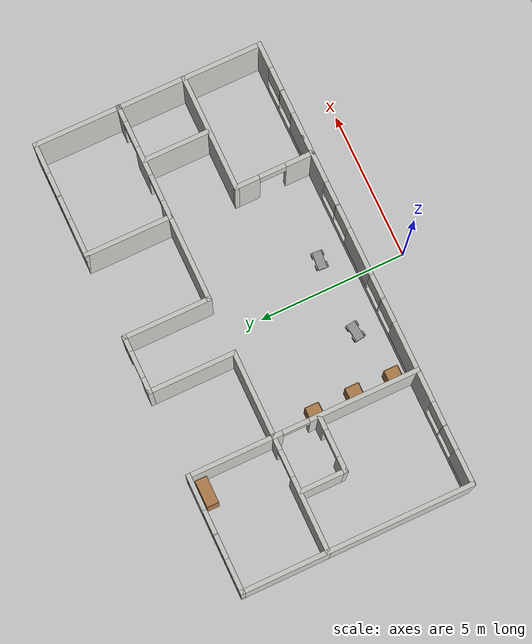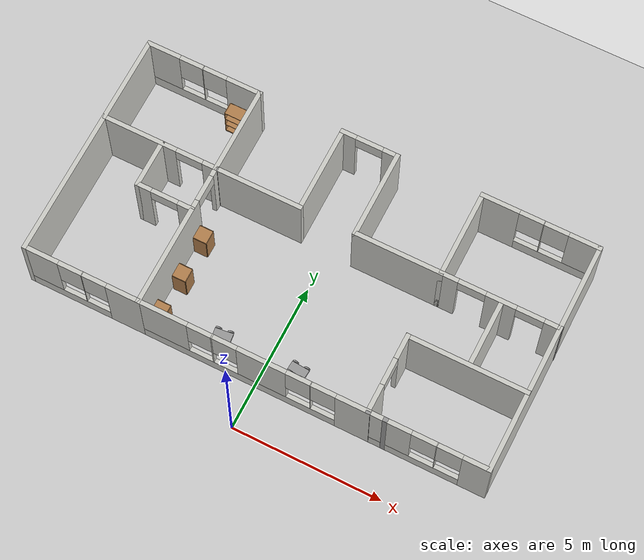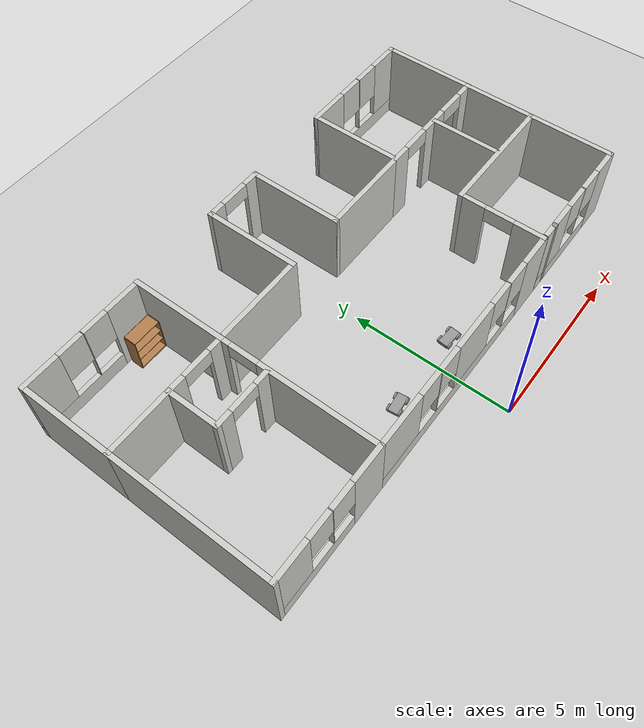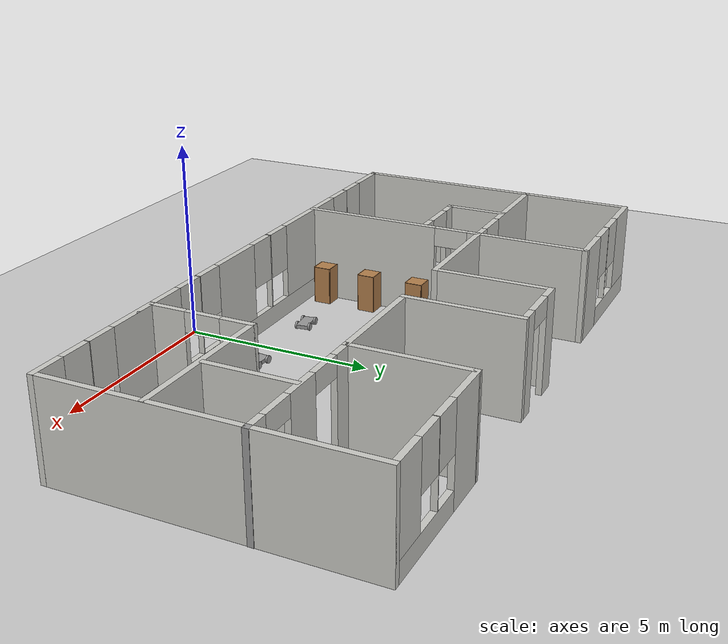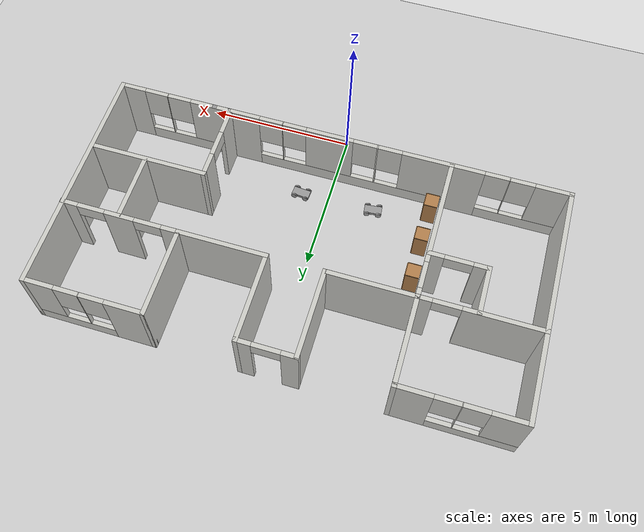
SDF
<sdf version="1.6">
 <world name="default">
  <plugin name="hello" filename="libhello.so"/>
  <light name="sun" type="directional">
   <pose>0 0 10 0 -0 0</pose>
   <diffuse>0.8 0.8 0.8 1</diffuse>
   <specular>0.2 0.2 0.2 1</specular>
   <attenuation>
    <range>1000</range>
    <constant>0.9</constant>
    <linear>0.01</linear>
    <quadratic>0.001</quadratic>
   </attenuation>
   <direction>-0.5 0.1 -0.9</direction>
  </light>
  <model name="ground_plane">
   <static>1</static>
   <link name="link">
    <collision name="collision">
     <geometry><plane><normal>0 0 1</normal><size>100 100</size></plane></geometry>
     <surface>
      <contact><collide_bitmask>65535</collide_bitmask></contact>
      <friction><ode><mu>100</mu><mu2>50</mu2></ode></friction>
     </surface>
    </collision>
    <visual name="visual">
     <cast_shadows>0</cast_shadows>
     <geometry><plane><normal>0 0 1</normal><size>100 100</size></plane></geometry>
     <material>
      <script><uri>file://media/materials/scripts/gazebo.material</uri><name>Gazebo/Grey</name></script>
     </material>
    </visual>
   </link>
  </model>
  <gravity>0 0 -9.8</gravity>
  <magnetic_field>6e-06 2.3e-05 -4.2e-05</magnetic_field>
  <atmosphere type="adiabatic"/>
  <physics name="default_physics" default="0" type="ode">
   <max_step_size>0.001</max_step_size>
   <real_time_factor>1</real_time_factor>
   <real_time_update_rate>1000</real_time_update_rate>
  </physics>
  <scene><ambient>0.4 0.4 0.4 1</ambient><background>0.7 0.7 0.7 1</background><shadows>1</shadows></scene>
  <spherical_coordinates>
   <surface_model>EARTH_WGS84</surface_model>
   <latitude_deg>0</latitude_deg>
   <longitude_deg>0</longitude_deg>
   <elevation>0</elevation>
   <heading_deg>0</heading_deg>
  </spherical_coordinates>
  <model name="MyOffice">
   <pose>-0.034703 5.38022 0 0 -0 0</pose>
   <link name="Wall_0">
    <pose>-0.005 3.85 0 0 -0 3.14159</pose>
    <visual name="Wall_0_Visual_0">
     <pose>-0.723973 0 1.25 0 -0 0</pose>
     <geometry><box><size>0.552053 0.15 2.5</size></box></geometry>
     <material>
      <script><uri>file://media/materials/scripts/gazebo.material</uri><name>Gazebo/CeilingTiled</name></script>
      <ambient>1 1 1 1</ambient>
     </material>
     <meta><layer>0</layer></meta>
    </visual>
    <collision name="Wall_0_Collision_0">
     <geometry><box><size>0.552053 0.15 2.5</size></box></geometry>
     <pose>-0.723973 0 1.25 0 -0 0</pose>
    </collision>
    <visual name="Wall_0_Visual_1">
     <pose>0.726027 0 1.25 0 -0 0</pose>
     <geometry><box><size>0.547947 0.15 2.5</size></box></geometry>
     <material>
      <script><uri>file://media/materials/scripts/gazebo.material</uri><name>Gazebo/CeilingTiled</name></script>
      <ambient>1 1 1 1</ambient>
     </material>
     <meta><layer>0</layer></meta>
    </visual>
    <collision name="Wall_0_Collision_1">
     <geometry><box><size>0.547947 0.15 2.5</size></box></geometry>
     <pose>0.726027 0 1.25 0 -0 0</pose>
    </collision>
    <visual name="Wall_0_Visual_2">
     <pose>0.002053 0 2.25 0 -0 0</pose>
     <geometry><box><size>0.9 0.15 0.5</size></box></geometry>
     <material>
      <script><uri>file://media/materials/scripts/gazebo.material</uri><name>Gazebo/CeilingTiled</name></script>
      <ambient>1 1 1 1</ambient>
     </material>
     <meta><layer>0</layer></meta>
    </visual>
    <collision name="Wall_0_Collision_2">
     <geometry><box><size>0.9 0.15 0.5</size></box></geometry>
     <pose>0.002053 0 2.25 0 -0 0</pose>
    </collision>
   </link>
   <link name="Wall_1">
    <collision name="Wall_1_Collision">
     <geometry><box><size>3 0.15 2.5</size></box></geometry>
     <pose>0 0 1.25 0 -0 0</pose>
    </collision>
    <visual name="Wall_1_Visual">
     <pose>0 0 1.25 0 -0 0</pose>
     <geometry><box><size>3 0.15 2.5</size></box></geometry>
     <material>
      <script><uri>file://media/materials/scripts/gazebo.material</uri><name>Gazebo/CeilingTiled</name></script>
      <ambient>1 1 1 1</ambient>
     </material>
     <meta><layer>0</layer></meta>
    </visual>
    <pose>-0.93 2.425 0 0 0 -1.5708</pose>
   </link>
   <link name="Wall_10">
    <collision name="Wall_10_Collision">
     <geometry><box><size>0.16 0.15 2.5</size></box></geometry>
     <pose>0 0 1.25 0 -0 0</pose>
    </collision>
    <visual name="Wall_10_Visual">
     <pose>0 0 1.25 0 -0 0</pose>
     <geometry><box><size>0.16 0.15 2.5</size></box></geometry>
     <material>
      <script><uri>file://media/materials/scripts/gazebo.material</uri><name>Gazebo/Grey</name></script>
      <ambient>1 1 1 1</ambient>
     </material>
     <meta><layer>0</layer></meta>
    </visual>
    <pose>3.775 -3.85 0 0 -0 0</pose>
   </link>
   <link name="Wall_14">
    <collision name="Wall_14_Collision">
     <geometry><box><size>5 0.15 2.5</size></box></geometry>
     <pose>0 0 1.25 0 -0 0</pose>
    </collision>
    <visual name="Wall_14_Visual">
     <pose>0 0 1.25 0 -0 0</pose>
     <geometry><box><size>5 0.15 2.5</size></box></geometry>
     <material>
      <script><uri>file://media/materials/scripts/gazebo.material</uri><name>Gazebo/CeilingTiled</name></script>
      <ambient>1 1 1 1</ambient>
     </material>
     <meta><layer>0</layer></meta>
    </visual>
    <pose>7.62 -1.425 0 0 0 -1.5708</pose>
   </link>
   <link name="Wall_15">
    <pose>5.695 -3.85 0 0 -0 3.14159</pose>
    <visual name="Wall_15_Visual_0">
     <pose>-1.54591 0 1.25 0 -0 0</pose>
     <geometry><box><size>0.908188 0.15 2.5</size></box></geometry>
     <material>
      <script><uri>file://media/materials/scripts/gazebo.material</uri><name>Gazebo/CeilingTiled</name></script>
      <ambient>1 1 1 1</ambient>
     </material>
     <meta><layer>0</layer></meta>
    </visual>
    <collision name="Wall_15_Collision_0">
     <geometry><box><size>0.908188 0.15 2.5</size></box></geometry>
     <pose>-1.54591 0 1.25 0 -0 0</pose>
    </collision>
    <visual name="Wall_15_Visual_1">
     <pose>0.454094 0 0.25 0 -0 0</pose>
     <geometry><box><size>3.09181 0.15 0.5</size></box></geometry>
     <material>
      <script><uri>file://media/materials/scripts/gazebo.material</uri><name>Gazebo/CeilingTiled</name></script>
      <ambient>1 1 1 1</ambient>
     </material>
     <meta><layer>0</layer></meta>
    </visual>
    <collision name="Wall_15_Collision_1">
     <geometry><box><size>3.09181 0.15 0.5</size></box></geometry>
     <pose>0.454094 0 0.25 0 -0 0</pose>
    </collision>
    <visual name="Wall_15_Visual_2">
     <pose>-0.280795 0 1.5 0 -0 0</pose>
     <geometry><box><size>0.022033 0.15 2</size></box></geometry>
     <material>
      <script><uri>file://media/materials/scripts/gazebo.material</uri><name>Gazebo/CeilingTiled</name></script>
      <ambient>1 1 1 1</ambient>
     </material>
     <meta><layer>0</layer></meta>
    </visual>
    <collision name="Wall_15_Collision_2">
     <geometry><box><size>0.022033 0.15 2</size></box></geometry>
     <pose>-0.280795 0 1.5 0 -0 0</pose>
    </collision>
    <visual name="Wall_15_Visual_3">
     <pose>1.26511 0 1.5 0 -0 0</pose>
     <geometry><box><size>1.46978 0.15 2</size></box></geometry>
     <material>
      <script><uri>file://media/materials/scripts/gazebo.material</uri><name>Gazebo/CeilingTiled</name></script>
      <ambient>1 1 1 1</ambient>
     </material>
     <meta><layer>0</layer></meta>
    </visual>
    <collision name="Wall_15_Collision_3">
     <geometry><box><size>1.46978 0.15 2</size></box></geometry>
     <pose>1.26511 0 1.5 0 -0 0</pose>
    </collision>
    <visual name="Wall_15_Visual_4">
     <pose>-0.691812 0 1.9 0 -0 0</pose>
     <geometry><box><size>0.8 0.15 1.2</size></box></geometry>
     <material>
      <script><uri>file://media/materials/scripts/gazebo.material</uri><name>Gazebo/CeilingTiled</name></script>
      <ambient>1 1 1 1</ambient>
     </material>
     <meta><layer>0</layer></meta>
    </visual>
    <collision name="Wall_15_Collision_4">
     <geometry><box><size>0.8 0.15 1.2</size></box></geometry>
     <pose>-0.691812 0 1.9 0 -0 0</pose>
    </collision>
    <visual name="Wall_15_Visual_5">
     <pose>0.130221 0 1.9 0 -0 0</pose>
     <geometry><box><size>0.8 0.15 1.2</size></box></geometry>
     <material>
      <script><uri>file://media/materials/scripts/gazebo.material</uri><name>Gazebo/CeilingTiled</name></script>
      <ambient>1 1 1 1</ambient>
     </material>
     <meta><layer>0</layer></meta>
    </visual>
    <collision name="Wall_15_Collision_5">
     <geometry><box><size>0.8 0.15 1.2</size></box></geometry>
     <pose>0.130221 0 1.9 0 -0 0</pose>
    </collision>
   </link>
   <link name="Wall_17">
    <collision name="Wall_17_Collision">
     <geometry><box><size>3 0.15 2.5</size></box></geometry>
     <pose>0 0 1.25 0 -0 0</pose>
    </collision>
    <visual name="Wall_17_Visual">
     <pose>0 0 1.25 0 -0 0</pose>
     <geometry><box><size>3 0.15 2.5</size></box></geometry>
     <material>
      <script><uri>file://media/materials/scripts/gazebo.material</uri><name>Gazebo/CeilingTiled</name></script>
      <ambient>1 1 1 1</ambient>
     </material>
     <meta><layer>0</layer></meta>
    </visual>
    <pose>3.77 2.425 0 0 -0 1.5708</pose>
   </link>
   <link name="Wall_18">
    <pose>5.695 3.85 0 0 -0 0</pose>
    <visual name="Wall_18_Visual_0">
     <pose>-1.34382 0 1.25 0 -0 0</pose>
     <geometry><box><size>1.31237 0.15 2.5</size></box></geometry>
     <material>
      <script><uri>file://media/materials/scripts/gazebo.material</uri><name>Gazebo/CeilingTiled</name></script>
      <ambient>1 1 1 1</ambient>
     </material>
     <meta><layer>0</layer></meta>
    </visual>
    <collision name="Wall_18_Collision_0">
     <geometry><box><size>1.31237 0.15 2.5</size></box></geometry>
     <pose>-1.34382 0 1.25 0 -0 0</pose>
    </collision>
    <visual name="Wall_18_Visual_1">
     <pose>0.656184 0 0.25 0 -0 0</pose>
     <geometry><box><size>2.68763 0.15 0.5</size></box></geometry>
     <material>
      <script><uri>file://media/materials/scripts/gazebo.material</uri><name>Gazebo/CeilingTiled</name></script>
      <ambient>1 1 1 1</ambient>
     </material>
     <meta><layer>0</layer></meta>
    </visual>
    <collision name="Wall_18_Collision_1">
     <geometry><box><size>2.68763 0.15 0.5</size></box></geometry>
     <pose>0.656184 0 0.25 0 -0 0</pose>
    </collision>
    <visual name="Wall_18_Visual_2">
     <pose>0.123384 0 1.5 0 -0 0</pose>
     <geometry><box><size>0.022033 0.15 2</size></box></geometry>
     <material>
      <script><uri>file://media/materials/scripts/gazebo.material</uri><name>Gazebo/CeilingTiled</name></script>
      <ambient>1 1 1 1</ambient>
     </material>
     <meta><layer>0</layer></meta>
    </visual>
    <collision name="Wall_18_Collision_2">
     <geometry><box><size>0.022033 0.15 2</size></box></geometry>
     <pose>0.123384 0 1.5 0 -0 0</pose>
    </collision>
    <visual name="Wall_18_Visual_3">
     <pose>1.4672 0 1.5 0 -0 0</pose>
     <geometry><box><size>1.0656 0.15 2</size></box></geometry>
     <material>
      <script><uri>file://media/materials/scripts/gazebo.material</uri><name>Gazebo/CeilingTiled</name></script>
      <ambient>1 1 1 1</ambient>
     </material>
     <meta><layer>0</layer></meta>
    </visual>
    <collision name="Wall_18_Collision_3">
     <geometry><box><size>1.0656 0.15 2</size></box></geometry>
     <pose>1.4672 0 1.5 0 -0 0</pose>
    </collision>
    <visual name="Wall_18_Visual_4">
     <pose>-0.287632 0 1.9 0 -0 0</pose>
     <geometry><box><size>0.8 0.15 1.2</size></box></geometry>
     <material>
      <script><uri>file://media/materials/scripts/gazebo.material</uri><name>Gazebo/CeilingTiled</name></script>
      <ambient>1 1 1 1</ambient>
     </material>
     <meta><layer>0</layer></meta>
    </visual>
    <collision name="Wall_18_Collision_4">
     <geometry><box><size>0.8 0.15 1.2</size></box></geometry>
     <pose>-0.287632 0 1.9 0 -0 0</pose>
    </collision>
    <visual name="Wall_18_Visual_5">
     <pose>0.534401 0 1.9 0 -0 0</pose>
     <geometry><box><size>0.8 0.15 1.2</size></box></geometry>
     <material>
      <script><uri>file://media/materials/scripts/gazebo.material</uri><name>Gazebo/CeilingTiled</name></script>
      <ambient>1 1 1 1</ambient>
     </material>
     <meta><layer>0</layer></meta>
    </visual>
    <collision name="Wall_18_Collision_5">
     <geometry><box><size>0.8 0.15 1.2</size></box></geometry>
     <pose>0.534401 0 1.9 0 -0 0</pose>
    </collision>
   </link>
   <link name="Wall_19">
    <collision name="Wall_19_Collision">
     <geometry><box><size>3 0.15 2.5</size></box></geometry>
     <pose>0 0 1.25 0 -0 0</pose>
    </collision>
    <visual name="Wall_19_Visual">
     <pose>0 0 1.25 0 -0 0</pose>
     <geometry><box><size>3 0.15 2.5</size></box></geometry>
     <material>
      <script><uri>file://media/materials/scripts/gazebo.material</uri><name>Gazebo/CeilingTiled</name></script>
      <ambient>1 1 1 1</ambient>
     </material>
     <meta><layer>0</layer></meta>
    </visual>
    <pose>7.62 2.425 0 0 0 -1.5708</pose>
   </link>
   <link name="Wall_2">
    <collision name="Wall_2_Collision">
     <geometry><box><size>3 0.15 2.5</size></box></geometry>
     <pose>0 0 1.25 0 -0 0</pose>
    </collision>
    <visual name="Wall_2_Visual">
     <pose>0 0 1.25 0 -0 0</pose>
     <geometry><box><size>3 0.15 2.5</size></box></geometry>
     <material>
      <script><uri>file://media/materials/scripts/gazebo.material</uri><name>Gazebo/CeilingTiled</name></script>
      <ambient>1 1 1 1</ambient>
     </material>
     <meta><layer>0</layer></meta>
    </visual>
    <pose>-2.355 1 0 0 -0 3.14159</pose>
   </link>
   <link name="Wall_21">
    <collision name="Wall_21_Collision">
     <geometry><box><size>4 0.15 2.5</size></box></geometry>
     <pose>0 0 1.25 0 -0 0</pose>
    </collision>
    <visual name="Wall_21_Visual">
     <pose>0 0 1.25 0 -0 0</pose>
     <geometry><box><size>4 0.15 2.5</size></box></geometry>
     <material>
      <script><uri>file://media/materials/scripts/gazebo.material</uri><name>Gazebo/CeilingTiled</name></script>
      <ambient>1 1 1 1</ambient>
     </material>
     <meta><layer>0</layer></meta>
    </visual>
    <pose>5.67839 -1.23961 0 0 -0 0</pose>
   </link>
   <link name="Wall_23">
    <pose>-0.005 -3.85 0 0 -0 3.14159</pose>
    <visual name="Wall_23_Visual_0">
     <pose>-3.29206 0 1.25 0 -0 0</pose>
     <geometry><box><size>1.11588 0.15 2.5</size></box></geometry>
     <material>
      <script><uri>file://media/materials/scripts/gazebo.material</uri><name>Gazebo/CeilingTiled</name></script>
      <ambient>1 1 1 1</ambient>
     </material>
     <meta><layer>0</layer></meta>
    </visual>
    <collision name="Wall_23_Collision_0">
     <geometry><box><size>1.11588 0.15 2.5</size></box></geometry>
     <pose>-3.29206 0 1.25 0 -0 0</pose>
    </collision>
    <visual name="Wall_23_Visual_1">
     <pose>0.557941 0 0.25 0 -0 0</pose>
     <geometry><box><size>6.58412 0.15 0.5</size></box></geometry>
     <material>
      <script><uri>file://media/materials/scripts/gazebo.material</uri><name>Gazebo/CeilingTiled</name></script>
      <ambient>1 1 1 1</ambient>
     </material>
     <meta><layer>0</layer></meta>
    </visual>
    <collision name="Wall_23_Collision_1">
     <geometry><box><size>6.58412 0.15 0.5</size></box></geometry>
     <pose>0.557941 0 0.25 0 -0 0</pose>
    </collision>
    <visual name="Wall_23_Visual_2">
     <pose>-1.9231 0 1.5 0 -0 0</pose>
     <geometry><box><size>0.022033 0.15 2</size></box></geometry>
     <material>
      <script><uri>file://media/materials/scripts/gazebo.material</uri><name>Gazebo/CeilingTiled</name></script>
      <ambient>1 1 1 1</ambient>
     </material>
     <meta><layer>0</layer></meta>
    </visual>
    <collision name="Wall_23_Collision_2">
     <geometry><box><size>0.022033 0.15 2</size></box></geometry>
     <pose>-1.9231 0 1.5 0 -0 0</pose>
    </collision>
    <visual name="Wall_23_Visual_3">
     <pose>-0.30527 0 1.5 0 -0 0</pose>
     <geometry><box><size>1.61363 0.15 2</size></box></geometry>
     <material>
      <script><uri>file://media/materials/scripts/gazebo.material</uri><name>Gazebo/CeilingTiled</name></script>
      <ambient>1 1 1 1</ambient>
     </material>
     <meta><layer>0</layer></meta>
    </visual>
    <collision name="Wall_23_Collision_3">
     <geometry><box><size>1.61363 0.15 2</size></box></geometry>
     <pose>-0.30527 0 1.5 0 -0 0</pose>
    </collision>
    <visual name="Wall_23_Visual_4">
     <pose>1.32131 0 1.5 0 -0 0</pose>
     <geometry><box><size>0.039523 0.15 2</size></box></geometry>
     <material>
      <script><uri>file://media/materials/scripts/gazebo.material</uri><name>Gazebo/CeilingTiled</name></script>
      <ambient>1 1 1 1</ambient>
     </material>
     <meta><layer>0</layer></meta>
    </visual>
    <collision name="Wall_23_Collision_4">
     <geometry><box><size>0.039523 0.15 2</size></box></geometry>
     <pose>1.32131 0 1.5 0 -0 0</pose>
    </collision>
    <visual name="Wall_23_Visual_5">
     <pose>2.99553 0 1.5 0 -0 0</pose>
     <geometry><box><size>1.70893 0.15 2</size></box></geometry>
     <material>
      <script><uri>file://media/materials/scripts/gazebo.material</uri><name>Gazebo/CeilingTiled</name></script>
      <ambient>1 1 1 1</ambient>
     </material>
     <meta><layer>0</layer></meta>
    </visual>
    <collision name="Wall_23_Collision_5">
     <geometry><box><size>1.70893 0.15 2</size></box></geometry>
     <pose>2.99553 0 1.5 0 -0 0</pose>
    </collision>
    <visual name="Wall_23_Visual_6">
     <pose>-2.33412 0 1.9 0 -0 0</pose>
     <geometry><box><size>0.8 0.15 1.2</size></box></geometry>
     <material>
      <script><uri>file://media/materials/scripts/gazebo.material</uri><name>Gazebo/CeilingTiled</name></script>
      <ambient>1 1 1 1</ambient>
     </material>
     <meta><layer>0</layer></meta>
    </visual>
    <collision name="Wall_23_Collision_6">
     <geometry><box><size>0.8 0.15 1.2</size></box></geometry>
     <pose>-2.33412 0 1.9 0 -0 0</pose>
    </collision>
    <visual name="Wall_23_Visual_7">
     <pose>-1.51208 0 1.9 0 -0 0</pose>
     <geometry><box><size>0.8 0.15 1.2</size></box></geometry>
     <material>
      <script><uri>file://media/materials/scripts/gazebo.material</uri><name>Gazebo/CeilingTiled</name></script>
      <ambient>1 1 1 1</ambient>
     </material>
     <meta><layer>0</layer></meta>
    </visual>
    <collision name="Wall_23_Collision_7">
     <geometry><box><size>0.8 0.15 1.2</size></box></geometry>
     <pose>-1.51208 0 1.9 0 -0 0</pose>
    </collision>
    <visual name="Wall_23_Visual_8">
     <pose>0.901544 0 1.9 0 -0 0</pose>
     <geometry><box><size>0.8 0.15 1.2</size></box></geometry>
     <material>
      <script><uri>file://media/materials/scripts/gazebo.material</uri><name>Gazebo/CeilingTiled</name></script>
      <ambient>1 1 1 1</ambient>
     </material>
     <meta><layer>0</layer></meta>
    </visual>
    <collision name="Wall_23_Collision_8">
     <geometry><box><size>0.8 0.15 1.2</size></box></geometry>
     <pose>0.901544 0 1.9 0 -0 0</pose>
    </collision>
    <visual name="Wall_23_Visual_9">
     <pose>1.74107 0 1.9 0 -0 0</pose>
     <geometry><box><size>0.8 0.15 1.2</size></box></geometry>
     <material>
      <script><uri>file://media/materials/scripts/gazebo.material</uri><name>Gazebo/CeilingTiled</name></script>
      <ambient>1 1 1 1</ambient>
     </material>
     <meta><layer>0</layer></meta>
    </visual>
    <collision name="Wall_23_Collision_9">
     <geometry><box><size>0.8 0.15 1.2</size></box></geometry>
     <pose>1.74107 0 1.9 0 -0 0</pose>
    </collision>
   </link>
   <link name="Wall_24">
    <pose>-5.705 -3.85 0 0 -0 3.14159</pose>
    <visual name="Wall_24_Visual_0">
     <pose>-1.42172 0 1.25 0 -0 0</pose>
     <geometry><box><size>1.15657 0.15 2.5</size></box></geometry>
     <material>
      <script><uri>file://media/materials/scripts/gazebo.material</uri><name>Gazebo/CeilingTiled</name></script>
      <ambient>0.760784 0.662745 0.627451 1</ambient>
     </material>
     <meta><layer>0</layer></meta>
    </visual>
    <collision name="Wall_24_Collision_0">
     <geometry><box><size>1.15657 0.15 2.5</size></box></geometry>
     <pose>-1.42172 0 1.25 0 -0 0</pose>
    </collision>
    <visual name="Wall_24_Visual_1">
     <pose>0.578285 0 0.25 0 -0 0</pose>
     <geometry><box><size>2.84343 0.15 0.5</size></box></geometry>
     <material>
      <script><uri>file://media/materials/scripts/gazebo.material</uri><name>Gazebo/CeilingTiled</name></script>
      <ambient>0.760784 0.662745 0.627451 1</ambient>
     </material>
     <meta><layer>0</layer></meta>
    </visual>
    <collision name="Wall_24_Collision_1">
     <geometry><box><size>2.84343 0.15 0.5</size></box></geometry>
     <pose>0.578285 0 0.25 0 -0 0</pose>
    </collision>
    <visual name="Wall_24_Visual_2">
     <pose>-0.032413 0 1.5 0 -0 0</pose>
     <geometry><box><size>0.022033 0.15 2</size></box></geometry>
     <material>
      <script><uri>file://media/materials/scripts/gazebo.material</uri><name>Gazebo/CeilingTiled</name></script>
      <ambient>0.760784 0.662745 0.627451 1</ambient>
     </material>
     <meta><layer>0</layer></meta>
    </visual>
    <collision name="Wall_24_Collision_2">
     <geometry><box><size>0.022033 0.15 2</size></box></geometry>
     <pose>-0.032413 0 1.5 0 -0 0</pose>
    </collision>
    <visual name="Wall_24_Visual_3">
     <pose>1.3893 0 1.5 0 -0 0</pose>
     <geometry><box><size>1.2214 0.15 2</size></box></geometry>
     <material>
      <script><uri>file://media/materials/scripts/gazebo.material</uri><name>Gazebo/CeilingTiled</name></script>
      <ambient>0.760784 0.662745 0.627451 1</ambient>
     </material>
     <meta><layer>0</layer></meta>
    </visual>
    <collision name="Wall_24_Collision_3">
     <geometry><box><size>1.2214 0.15 2</size></box></geometry>
     <pose>1.3893 0 1.5 0 -0 0</pose>
    </collision>
    <visual name="Wall_24_Visual_4">
     <pose>-0.44343 0 1.9 0 -0 0</pose>
     <geometry><box><size>0.8 0.15 1.2</size></box></geometry>
     <material>
      <script><uri>file://media/materials/scripts/gazebo.material</uri><name>Gazebo/CeilingTiled</name></script>
      <ambient>0.760784 0.662745 0.627451 1</ambient>
     </material>
     <meta><layer>0</layer></meta>
    </visual>
    <collision name="Wall_24_Collision_4">
     <geometry><box><size>0.8 0.15 1.2</size></box></geometry>
     <pose>-0.44343 0 1.9 0 -0 0</pose>
    </collision>
    <visual name="Wall_24_Visual_5">
     <pose>0.378603 0 1.9 0 -0 0</pose>
     <geometry><box><size>0.8 0.15 1.2</size></box></geometry>
     <material>
      <script><uri>file://media/materials/scripts/gazebo.material</uri><name>Gazebo/CeilingTiled</name></script>
      <ambient>0.760784 0.662745 0.627451 1</ambient>
     </material>
     <meta><layer>0</layer></meta>
    </visual>
    <collision name="Wall_24_Collision_5">
     <geometry><box><size>0.8 0.15 1.2</size></box></geometry>
     <pose>0.378603 0 1.9 0 -0 0</pose>
    </collision>
   </link>
   <link name="Wall_3">
    <pose>-3.78 -1.425 0 0 0 -1.5708</pose>
    <visual name="Wall_3_Visual_0">
     <pose>-2.31536 0 1.25 0 -0 0</pose>
     <geometry><box><size>0.36928 0.15 2.5</size></box></geometry>
     <material>
      <script><uri>file://media/materials/scripts/gazebo.material</uri><name>Gazebo/CeilingTiled</name></script>
      <ambient>0.760784 0.662745 0.627451 1</ambient>
     </material>
     <meta><layer>0</layer></meta>
    </visual>
    <collision name="Wall_3_Collision_0">
     <geometry><box><size>0.36928 0.15 2.5</size></box></geometry>
     <pose>-2.31536 0 1.25 0 -0 0</pose>
    </collision>
    <visual name="Wall_3_Visual_1">
     <pose>0.63464 0 1.25 0 -0 0</pose>
     <geometry><box><size>3.73072 0.15 2.5</size></box></geometry>
     <material>
      <script><uri>file://media/materials/scripts/gazebo.material</uri><name>Gazebo/CeilingTiled</name></script>
      <ambient>0.760784 0.662745 0.627451 1</ambient>
     </material>
     <meta><layer>0</layer></meta>
    </visual>
    <collision name="Wall_3_Collision_1">
     <geometry><box><size>3.73072 0.15 2.5</size></box></geometry>
     <pose>0.63464 0 1.25 0 -0 0</pose>
    </collision>
    <visual name="Wall_3_Visual_2">
     <pose>-1.68072 0 2.25 0 -0 0</pose>
     <geometry><box><size>0.9 0.15 0.5</size></box></geometry>
     <material>
      <script><uri>file://media/materials/scripts/gazebo.material</uri><name>Gazebo/CeilingTiled</name></script>
      <ambient>0.760784 0.662745 0.627451 1</ambient>
     </material>
     <meta><layer>0</layer></meta>
    </visual>
    <collision name="Wall_3_Collision_2">
     <geometry><box><size>0.9 0.15 0.5</size></box></geometry>
     <pose>-1.68072 0 2.25 0 -0 0</pose>
    </collision>
   </link>
   <link name="Wall_32">
    <collision name="Wall_32_Collision">
     <geometry><box><size>3 0.15 2.5</size></box></geometry>
     <pose>0 0 1.25 0 -0 0</pose>
    </collision>
    <visual name="Wall_32_Visual">
     <pose>0 0 1.25 0 -0 0</pose>
     <geometry><box><size>3 0.15 2.5</size></box></geometry>
     <material>
      <script><uri>file://media/materials/scripts/gazebo.material</uri><name>Gazebo/CeilingTiled</name></script>
      <ambient>1 1 1 1</ambient>
     </material>
     <meta><layer>0</layer></meta>
    </visual>
    <pose>-3.78 2.425 0 0 -0 1.5708</pose>
   </link>
   <link name="Wall_33">
    <pose>-5.705 3.85 0 0 -0 3.14159</pose>
    <visual name="Wall_33_Visual_0">
     <pose>-1.39548 0 1.25 0 -0 0</pose>
     <geometry><box><size>1.20904 0.15 2.5</size></box></geometry>
     <material>
      <script><uri>file://media/materials/scripts/gazebo.material</uri><name>Gazebo/CeilingTiled</name></script>
      <ambient>1 1 1 1</ambient>
     </material>
     <meta><layer>0</layer></meta>
    </visual>
    <collision name="Wall_33_Collision_0">
     <geometry><box><size>1.20904 0.15 2.5</size></box></geometry>
     <pose>-1.39548 0 1.25 0 -0 0</pose>
    </collision>
    <visual name="Wall_33_Visual_1">
     <pose>0.60452 0 0.25 0 -0 0</pose>
     <geometry><box><size>2.79096 0.15 0.5</size></box></geometry>
     <material>
      <script><uri>file://media/materials/scripts/gazebo.material</uri><name>Gazebo/CeilingTiled</name></script>
      <ambient>1 1 1 1</ambient>
     </material>
     <meta><layer>0</layer></meta>
    </visual>
    <collision name="Wall_33_Collision_1">
     <geometry><box><size>2.79096 0.15 0.5</size></box></geometry>
     <pose>0.60452 0 0.25 0 -0 0</pose>
    </collision>
    <visual name="Wall_33_Visual_2">
     <pose>0.020057 0 1.5 0 -0 0</pose>
     <geometry><box><size>0.022033 0.15 2</size></box></geometry>
     <material>
      <script><uri>file://media/materials/scripts/gazebo.material</uri><name>Gazebo/CeilingTiled</name></script>
      <ambient>1 1 1 1</ambient>
     </material>
     <meta><layer>0</layer></meta>
    </visual>
    <collision name="Wall_33_Collision_2">
     <geometry><box><size>0.022033 0.15 2</size></box></geometry>
     <pose>0.020057 0 1.5 0 -0 0</pose>
    </collision>
    <visual name="Wall_33_Visual_3">
     <pose>1.41554 0 1.5 0 -0 0</pose>
     <geometry><box><size>1.16893 0.15 2</size></box></geometry>
     <material>
      <script><uri>file://media/materials/scripts/gazebo.material</uri><name>Gazebo/CeilingTiled</name></script>
      <ambient>1 1 1 1</ambient>
     </material>
     <meta><layer>0</layer></meta>
    </visual>
    <collision name="Wall_33_Collision_3">
     <geometry><box><size>1.16893 0.15 2</size></box></geometry>
     <pose>1.41554 0 1.5 0 -0 0</pose>
    </collision>
    <visual name="Wall_33_Visual_4">
     <pose>-0.39096 0 1.9 0 -0 0</pose>
     <geometry><box><size>0.8 0.15 1.2</size></box></geometry>
     <material>
      <script><uri>file://media/materials/scripts/gazebo.material</uri><name>Gazebo/CeilingTiled</name></script>
      <ambient>1 1 1 1</ambient>
     </material>
     <meta><layer>0</layer></meta>
    </visual>
    <collision name="Wall_33_Collision_4">
     <geometry><box><size>0.8 0.15 1.2</size></box></geometry>
     <pose>-0.39096 0 1.9 0 -0 0</pose>
    </collision>
    <visual name="Wall_33_Visual_5">
     <pose>0.431073 0 1.9 0 -0 0</pose>
     <geometry><box><size>0.8 0.15 1.2</size></box></geometry>
     <material>
      <script><uri>file://media/materials/scripts/gazebo.material</uri><name>Gazebo/CeilingTiled</name></script>
      <ambient>1 1 1 1</ambient>
     </material>
     <meta><layer>0</layer></meta>
    </visual>
    <collision name="Wall_33_Collision_5">
     <geometry><box><size>0.8 0.15 1.2</size></box></geometry>
     <pose>0.431073 0 1.9 0 -0 0</pose>
    </collision>
   </link>
   <link name="Wall_34">
    <collision name="Wall_34_Collision">
     <geometry><box><size>3 0.15 2.5</size></box></geometry>
     <pose>0 0 1.25 0 -0 0</pose>
    </collision>
    <visual name="Wall_34_Visual">
     <pose>0 0 1.25 0 -0 0</pose>
     <geometry><box><size>3 0.15 2.5</size></box></geometry>
     <material>
      <script><uri>file://media/materials/scripts/gazebo.material</uri><name>Gazebo/CeilingTiled</name></script>
      <ambient>1 1 1 1</ambient>
     </material>
     <meta><layer>0</layer></meta>
    </visual>
    <pose>-7.63 2.425 0 0 0 -1.5708</pose>
   </link>
   <link name="Wall_35">
    <pose>-5.705 1 0 0 -0 0</pose>
    <visual name="Wall_35_Visual_0">
     <pose>-0.711654 0 1.25 0 -0 0</pose>
     <geometry><box><size>2.57669 0.15 2.5</size></box></geometry>
     <material>
      <script><uri>file://media/materials/scripts/gazebo.material</uri><name>Gazebo/CeilingTiled</name></script>
      <ambient>0.760784 0.662745 0.627451 1</ambient>
     </material>
     <meta><layer>0</layer></meta>
    </visual>
    <collision name="Wall_35_Collision_0">
     <geometry><box><size>2.57669 0.15 2.5</size></box></geometry>
     <pose>-0.711654 0 1.25 0 -0 0</pose>
    </collision>
    <visual name="Wall_35_Visual_1">
     <pose>1.73835 0 1.25 0 -0 0</pose>
     <geometry><box><size>0.523307 0.15 2.5</size></box></geometry>
     <material>
      <script><uri>file://media/materials/scripts/gazebo.material</uri><name>Gazebo/CeilingTiled</name></script>
      <ambient>0.760784 0.662745 0.627451 1</ambient>
     </material>
     <meta><layer>0</layer></meta>
    </visual>
    <collision name="Wall_35_Collision_1">
     <geometry><box><size>0.523307 0.15 2.5</size></box></geometry>
     <pose>1.73835 0 1.25 0 -0 0</pose>
    </collision>
    <visual name="Wall_35_Visual_2">
     <pose>1.02669 0 2.25 0 -0 0</pose>
     <geometry><box><size>0.9 0.15 0.5</size></box></geometry>
     <material>
      <script><uri>file://media/materials/scripts/gazebo.material</uri><name>Gazebo/CeilingTiled</name></script>
      <ambient>0.760784 0.662745 0.627451 1</ambient>
     </material>
     <meta><layer>0</layer></meta>
    </visual>
    <collision name="Wall_35_Collision_2">
     <geometry><box><size>0.9 0.15 0.5</size></box></geometry>
     <pose>1.02669 0 2.25 0 -0 0</pose>
    </collision>
   </link>
   <link name="Wall_36">
    <collision name="Wall_36_Collision">
     <geometry><box><size>0.16 0.15 2.5</size></box></geometry>
     <pose>0 0 1.25 0 -0 0</pose>
    </collision>
    <visual name="Wall_36_Visual">
     <pose>0 0 1.25 0 -0 0</pose>
     <geometry><box><size>0.16 0.15 2.5</size></box></geometry>
     <material>
      <script><uri>file://media/materials/scripts/gazebo.material</uri><name>Gazebo/Grey</name></script>
      <ambient>1 1 1 1</ambient>
     </material>
     <meta><layer>0</layer></meta>
    </visual>
    <pose>-3.775 1 0 0 -0 0</pose>
   </link>
   <link name="Wall_38">
    <pose>-4.70983 -0.522516 0 0 -0 3.14159</pose>
    <visual name="Wall_38_Visual_0">
     <pose>-0.725551 0 1.25 0 -0 0</pose>
     <geometry><box><size>0.548898 0.15 2.5</size></box></geometry>
     <material>
      <script><uri>file://media/materials/scripts/gazebo.material</uri><name>Gazebo/CeilingTiled</name></script>
      <ambient>1 1 1 1</ambient>
     </material>
     <meta><layer>0</layer></meta>
    </visual>
    <collision name="Wall_38_Collision_0">
     <geometry><box><size>0.548898 0.15 2.5</size></box></geometry>
     <pose>-0.725551 0 1.25 0 -0 0</pose>
    </collision>
    <visual name="Wall_38_Visual_1">
     <pose>0.724449 0 1.25 0 -0 0</pose>
     <geometry><box><size>0.551102 0.15 2.5</size></box></geometry>
     <material>
      <script><uri>file://media/materials/scripts/gazebo.material</uri><name>Gazebo/CeilingTiled</name></script>
      <ambient>1 1 1 1</ambient>
     </material>
     <meta><layer>0</layer></meta>
    </visual>
    <collision name="Wall_38_Collision_1">
     <geometry><box><size>0.551102 0.15 2.5</size></box></geometry>
     <pose>0.724449 0 1.25 0 -0 0</pose>
    </collision>
    <visual name="Wall_38_Visual_2">
     <pose>-0.001102 0 2.25 0 -0 0</pose>
     <geometry><box><size>0.9 0.15 0.5</size></box></geometry>
     <material>
      <script><uri>file://media/materials/scripts/gazebo.material</uri><name>Gazebo/CeilingTiled</name></script>
      <ambient>1 1 1 1</ambient>
     </material>
     <meta><layer>0</layer></meta>
    </visual>
    <collision name="Wall_38_Collision_2">
     <geometry><box><size>0.9 0.15 0.5</size></box></geometry>
     <pose>-0.001102 0 2.25 0 -0 0</pose>
    </collision>
   </link>
   <link name="Wall_39">
    <collision name="Wall_39_Collision">
     <geometry><box><size>1.65 0.15 2.5</size></box></geometry>
     <pose>0 0 1.25 0 -0 0</pose>
    </collision>
    <visual name="Wall_39_Visual">
     <pose>0 0 1.25 0 -0 0</pose>
     <geometry><box><size>1.65 0.15 2.5</size></box></geometry>
     <material>
      <script><uri>file://media/materials/scripts/gazebo.material</uri><name>Gazebo/CeilingTiled</name></script>
      <ambient>1 1 1 1</ambient>
     </material>
     <meta><layer>0</layer></meta>
    </visual>
    <pose>-5.63483 0.227484 0 0 -0 1.5708</pose>
   </link>
   <link name="Wall_41">
    <collision name="Wall_41_Collision">
     <geometry><box><size>5 0.15 2.5</size></box></geometry>
     <pose>0 0 1.25 0 -0 0</pose>
    </collision>
    <visual name="Wall_41_Visual">
     <pose>0 0 1.25 0 -0 0</pose>
     <geometry><box><size>5 0.15 2.5</size></box></geometry>
     <material>
      <script><uri>file://media/materials/scripts/gazebo.material</uri><name>Gazebo/CeilingTiled</name></script>
      <ambient>0.760784 0.662745 0.627451 1</ambient>
     </material>
     <meta><layer>0</layer></meta>
    </visual>
    <pose>-7.63 -1.425 0 0 0 -1.5708</pose>
   </link>
   <link name="Wall_43">
    <pose>5.695 1 0 0 -0 0</pose>
    <visual name="Wall_43_Visual_0">
     <pose>-1.68173 0 1.25 0 -0 0</pose>
     <geometry><box><size>0.636535 0.15 2.5</size></box></geometry>
     <material>
      <script><uri>file://media/materials/scripts/gazebo.material</uri><name>Gazebo/CeilingTiled</name></script>
      <ambient>1 1 1 1</ambient>
     </material>
     <meta><layer>0</layer></meta>
    </visual>
    <collision name="Wall_43_Collision_0">
     <geometry><box><size>0.636535 0.15 2.5</size></box></geometry>
     <pose>-1.68173 0 1.25 0 -0 0</pose>
    </collision>
    <visual name="Wall_43_Visual_1">
     <pose>0.029478 0 1.25 0 -0 0</pose>
     <geometry><box><size>0.985885 0.15 2.5</size></box></geometry>
     <material>
      <script><uri>file://media/materials/scripts/gazebo.material</uri><name>Gazebo/CeilingTiled</name></script>
      <ambient>1 1 1 1</ambient>
     </material>
     <meta><layer>0</layer></meta>
    </visual>
    <collision name="Wall_43_Collision_1">
     <geometry><box><size>0.985885 0.15 2.5</size></box></geometry>
     <pose>0.029478 0 1.25 0 -0 0</pose>
    </collision>
    <visual name="Wall_43_Visual_2">
     <pose>1.71121 0 1.25 0 -0 0</pose>
     <geometry><box><size>0.57758 0.15 2.5</size></box></geometry>
     <material>
      <script><uri>file://media/materials/scripts/gazebo.material</uri><name>Gazebo/CeilingTiled</name></script>
      <ambient>1 1 1 1</ambient>
     </material>
     <meta><layer>0</layer></meta>
    </visual>
    <collision name="Wall_43_Collision_2">
     <geometry><box><size>0.57758 0.15 2.5</size></box></geometry>
     <pose>1.71121 0 1.25 0 -0 0</pose>
    </collision>
    <visual name="Wall_43_Visual_3">
     <pose>-0.913465 0 2.25 0 -0 0</pose>
     <geometry><box><size>0.9 0.15 0.5</size></box></geometry>
     <material>
      <script><uri>file://media/materials/scripts/gazebo.material</uri><name>Gazebo/CeilingTiled</name></script>
      <ambient>1 1 1 1</ambient>
     </material>
     <meta><layer>0</layer></meta>
    </visual>
    <collision name="Wall_43_Collision_3">
     <geometry><box><size>0.9 0.15 0.5</size></box></geometry>
     <pose>-0.913465 0 2.25 0 -0 0</pose>
    </collision>
    <visual name="Wall_43_Visual_4">
     <pose>0.97242 0 2.25 0 -0 0</pose>
     <geometry><box><size>0.9 0.15 0.5</size></box></geometry>
     <material>
      <script><uri>file://media/materials/scripts/gazebo.material</uri><name>Gazebo/CeilingTiled</name></script>
      <ambient>1 1 1 1</ambient>
     </material>
     <meta><layer>0</layer></meta>
    </visual>
    <collision name="Wall_43_Collision_4">
     <geometry><box><size>0.9 0.15 0.5</size></box></geometry>
     <pose>0.97242 0 2.25 0 -0 0</pose>
    </collision>
   </link>
   <link name="Wall_44">
    <collision name="Wall_44_Collision">
     <geometry><box><size>0.16 0.15 2.5</size></box></geometry>
     <pose>0 0 1.25 0 -0 0</pose>
    </collision>
    <visual name="Wall_44_Visual">
     <pose>0 0 1.25 0 -0 0</pose>
     <geometry><box><size>0.16 0.15 2.5</size></box></geometry>
     <material>
      <script><uri>file://media/materials/scripts/gazebo.material</uri><name>Gazebo/Grey</name></script>
      <ambient>1 1 1 1</ambient>
     </material>
     <meta><layer>0</layer></meta>
    </visual>
    <pose>7.625 1 0 0 -0 0</pose>
   </link>
   <link name="Wall_46">
    <collision name="Wall_46_Collision">
     <geometry><box><size>2.25 0.15 2.5</size></box></geometry>
     <pose>0 0 1.25 0 -0 0</pose>
    </collision>
    <visual name="Wall_46_Visual">
     <pose>0 0 1.25 0 -0 0</pose>
     <geometry><box><size>2.25 0.15 2.5</size></box></geometry>
     <material>
      <script><uri>file://media/materials/scripts/gazebo.material</uri><name>Gazebo/CeilingTiled</name></script>
      <ambient>1 1 1 1</ambient>
     </material>
     <meta><layer>0</layer></meta>
    </visual>
    <pose>5.74726 -0.103351 0 0 0 -1.5708</pose>
   </link>
   <link name="Wall_48">
    <pose>3.75339 -2.53961 0 0 0 -1.5708</pose>
    <visual name="Wall_48_Visual_0">
     <pose>-0.943114 0 1.25 0 -0 0</pose>
     <geometry><box><size>0.863773 0.15 2.5</size></box></geometry>
     <material>
      <script><uri>file://media/materials/scripts/gazebo.material</uri><name>Gazebo/CeilingTiled</name></script>
      <ambient>1 1 1 1</ambient>
     </material>
     <meta><layer>0</layer></meta>
    </visual>
    <collision name="Wall_48_Collision_0">
     <geometry><box><size>0.863773 0.15 2.5</size></box></geometry>
     <pose>-0.943114 0 1.25 0 -0 0</pose>
    </collision>
    <visual name="Wall_48_Visual_1">
     <pose>0.881886 0 1.25 0 -0 0</pose>
     <geometry><box><size>0.986227 0.15 2.5</size></box></geometry>
     <material>
      <script><uri>file://media/materials/scripts/gazebo.material</uri><name>Gazebo/CeilingTiled</name></script>
      <ambient>1 1 1 1</ambient>
     </material>
     <meta><layer>0</layer></meta>
    </visual>
    <collision name="Wall_48_Collision_1">
     <geometry><box><size>0.986227 0.15 2.5</size></box></geometry>
     <pose>0.881886 0 1.25 0 -0 0</pose>
    </collision>
    <visual name="Wall_48_Visual_2">
     <pose>-0.061227 0 2.25 0 -0 0</pose>
     <geometry><box><size>0.9 0.15 0.5</size></box></geometry>
     <material>
      <script><uri>file://media/materials/scripts/gazebo.material</uri><name>Gazebo/CeilingTiled</name></script>
      <ambient>1 1 1 1</ambient>
     </material>
     <meta><layer>0</layer></meta>
    </visual>
    <collision name="Wall_48_Collision_2">
     <geometry><box><size>0.9 0.15 0.5</size></box></geometry>
     <pose>-0.061227 0 2.25 0 -0 0</pose>
    </collision>
   </link>
   <link name="Wall_5">
    <collision name="Wall_5_Collision">
     <geometry><box><size>0.15 0.15 2.5</size></box></geometry>
     <pose>0 0 1.25 0 -0 0</pose>
    </collision>
    <visual name="Wall_5_Visual">
     <pose>0 0 1.25 0 -0 0</pose>
     <geometry><box><size>0.15 0.15 2.5</size></box></geometry>
     <material>
      <script><uri>file://media/materials/scripts/gazebo.material</uri><name>Gazebo/Grey</name></script>
      <ambient>1 1 1 1</ambient>
     </material>
     <meta><layer>0</layer></meta>
    </visual>
    <pose>4.32 -3.85 0 0 -0 0</pose>
   </link>
   <link name="Wall_7">
    <collision name="Wall_7_Collision">
     <geometry><box><size>3 0.15 2.5</size></box></geometry>
     <pose>0 0 1.25 0 -0 0</pose>
    </collision>
    <visual name="Wall_7_Visual">
     <pose>0 0 1.25 0 -0 0</pose>
     <geometry><box><size>3 0.15 2.5</size></box></geometry>
     <material>
      <script><uri>file://media/materials/scripts/gazebo.material</uri><name>Gazebo/CeilingTiled</name></script>
      <ambient>1 1 1 1</ambient>
     </material>
     <meta><layer>0</layer></meta>
    </visual>
    <pose>0.92 2.425 0 0 0 -1.5708</pose>
   </link>
   <link name="Wall_8">
    <collision name="Wall_8_Collision">
     <geometry><box><size>3 0.15 2.5</size></box></geometry>
     <pose>0 0 1.25 0 -0 0</pose>
    </collision>
    <visual name="Wall_8_Visual">
     <pose>0 0 1.25 0 -0 0</pose>
     <geometry><box><size>3 0.15 2.5</size></box></geometry>
     <material>
      <script><uri>file://media/materials/scripts/gazebo.material</uri><name>Gazebo/CeilingTiled</name></script>
      <ambient>1 1 1 1</ambient>
     </material>
     <meta><layer>0</layer></meta>
    </visual>
    <pose>2.345 1 0 0 -0 0</pose>
   </link>
   <static>1</static>
  </model>
  <model name="cabinet">
   <static>1</static>
   <link name="cabinet_bottom_plate">
    <inertial>
     <pose>0 0 -1 0 -0 0</pose>
     <inertia><ixx>2.05</ixx><ixy>0</ixy><ixz>0</ixz><iyy>2.05</iyy><iyz>0</iyz><izz>2.05</izz></inertia>
     <mass>25</mass>
    </inertial>
    <collision name="cabinet_bottom_plate_geom">
     <pose>0 0 0.01 0 -0 0</pose>
     <geometry><box><size>0.45 0.45 0.02</size></box></geometry>
    </collision>
    <visual name="cabinet_bottom_plate_geom_visual">
     <pose>0 0 0.01 0 -0 0</pose>
     <geometry><box><size>0.45 0.45 0.02</size></box></geometry>
     <material>
      <script><uri>file://media/materials/scripts/gazebo.material</uri><name>Gazebo/Wood</name></script>
     </material>
    </visual>
    <collision name="cabinet_bottom_plate_geom_cabinet_back_plate">
     <pose>0.235 0 0.51 0 -0 0</pose>
     <geometry><box><size>0.02 0.45 1.02</size></box></geometry>
    </collision>
    <visual name="cabinet_bottom_plate_geom_cabinet_back_plate_visual">
     <pose>0.235 0 0.51 0 -0 0</pose>
     <geometry><box><size>0.02 0.45 1.02</size></box></geometry>
     <material>
      <script><uri>file://media/materials/scripts/gazebo.material</uri><name>Gazebo/Wood</name></script>
     </material>
    </visual>
    <collision name="cabinet_bottom_plate_geom_cabinet_left_plate">
     <pose>0 0.235 0.51 0 -0 0</pose>
     <geometry><box><size>0.45 0.02 1.02</size></box></geometry>
    </collision>
    <visual name="cabinet_bottom_plate_geom_cabinet_left_plate_visual">
     <pose>0 0.235 0.51 0 -0 0</pose>
     <geometry><box><size>0.45 0.02 1.02</size></box></geometry>
     <material>
      <script><uri>file://media/materials/scripts/gazebo.material</uri><name>Gazebo/Wood</name></script>
     </material>
    </visual>
    <collision name="cabinet_bottom_plate_geom_cabinet_middle_plate">
     <pose>0 0 0.51 0 -0 0</pose>
     <geometry><box><size>0.45 0.45 0.02</size></box></geometry>
    </collision>
    <visual name="cabinet_bottom_plate_geom_cabinet_middle_plate_visual">
     <pose>0 0 0.51 0 -0 0</pose>
     <geometry><box><size>0.45 0.45 0.02</size></box></geometry>
     <material>
      <script><uri>file://media/materials/scripts/gazebo.material</uri><name>Gazebo/Wood</name></script>
     </material>
    </visual>
    <collision name="cabinet_bottom_plate_geom_cabinet_right_plate">
     <pose>0 -0.235 0.51 0 -0 0</pose>
     <geometry><box><size>0.45 0.02 1.02</size></box></geometry>
    </collision>
    <visual name="cabinet_bottom_plate_geom_cabinet_right_plate_visual">
     <pose>0 -0.235 0.51 0 -0 0</pose>
     <geometry><box><size>0.45 0.02 1.02</size></box></geometry>
     <material>
      <script><uri>file://media/materials/scripts/gazebo.material</uri><name>Gazebo/Wood</name></script>
     </material>
    </visual>
    <collision name="cabinet_bottom_plate_geom_cabinet_top_plate">
     <pose>0 0 1.01 0 -0 0</pose>
     <geometry><box><size>0.45 0.45 0.02</size></box></geometry>
    </collision>
    <visual name="cabinet_bottom_plate_geom_cabinet_top_plate_visual">
     <pose>0 0 1.01 0 -0 0</pose>
     <geometry><box><size>0.45 0.45 0.02</size></box></geometry>
     <material>
      <script><uri>file://media/materials/scripts/gazebo.material</uri><name>Gazebo/Wood</name></script>
     </material>
    </visual>
   </link>
   <pose>-3.47932 2.07525 0 0 -0 0</pose>
  </model>
  <model name="cabinet_0">
   <static>1</static>
   <link name="cabinet_bottom_plate">
    <inertial>
     <pose>0 0 -1 0 -0 0</pose>
     <inertia><ixx>2.05</ixx><ixy>0</ixy><ixz>0</ixz><iyy>2.05</iyy><iyz>0</iyz><izz>2.05</izz></inertia>
     <mass>25</mass>
    </inertial>
    <collision name="cabinet_bottom_plate_geom">
     <pose>0 0 0.01 0 -0 0</pose>
     <geometry><box><size>0.45 0.45 0.02</size></box></geometry>
    </collision>
    <visual name="cabinet_bottom_plate_geom_visual">
     <pose>0 0 0.01 0 -0 0</pose>
     <geometry><box><size>0.45 0.45 0.02</size></box></geometry>
     <material>
      <script><uri>file://media/materials/scripts/gazebo.material</uri><name>Gazebo/Wood</name></script>
     </material>
    </visual>
    <collision name="cabinet_bottom_plate_geom_cabinet_back_plate">
     <pose>0.235 0 0.51 0 -0 0</pose>
     <geometry><box><size>0.02 0.45 1.02</size></box></geometry>
    </collision>
    <visual name="cabinet_bottom_plate_geom_cabinet_back_plate_visual">
     <pose>0.235 0 0.51 0 -0 0</pose>
     <geometry><box><size>0.02 0.45 1.02</size></box></geometry>
     <material>
      <script><uri>file://media/materials/scripts/gazebo.material</uri><name>Gazebo/Wood</name></script>
     </material>
    </visual>
    <collision name="cabinet_bottom_plate_geom_cabinet_left_plate">
     <pose>0 0.235 0.51 0 -0 0</pose>
     <geometry><box><size>0.45 0.02 1.02</size></box></geometry>
    </collision>
    <visual name="cabinet_bottom_plate_geom_cabinet_left_plate_visual">
     <pose>0 0.235 0.51 0 -0 0</pose>
     <geometry><box><size>0.45 0.02 1.02</size></box></geometry>
     <material>
      <script><uri>file://media/materials/scripts/gazebo.material</uri><name>Gazebo/Wood</name></script>
     </material>
    </visual>
    <collision name="cabinet_bottom_plate_geom_cabinet_middle_plate">
     <pose>0 0 0.51 0 -0 0</pose>
     <geometry><box><size>0.45 0.45 0.02</size></box></geometry>
    </collision>
    <visual name="cabinet_bottom_plate_geom_cabinet_middle_plate_visual">
     <pose>0 0 0.51 0 -0 0</pose>
     <geometry><box><size>0.45 0.45 0.02</size></box></geometry>
     <material>
      <script><uri>file://media/materials/scripts/gazebo.material</uri><name>Gazebo/Wood</name></script>
     </material>
    </visual>
    <collision name="cabinet_bottom_plate_geom_cabinet_right_plate">
     <pose>0 -0.235 0.51 0 -0 0</pose>
     <geometry><box><size>0.45 0.02 1.02</size></box></geometry>
    </collision>
    <visual name="cabinet_bottom_plate_geom_cabinet_right_plate_visual">
     <pose>0 -0.235 0.51 0 -0 0</pose>
     <geometry><box><size>0.45 0.02 1.02</size></box></geometry>
     <material>
      <script><uri>file://media/materials/scripts/gazebo.material</uri><name>Gazebo/Wood</name></script>
     </material>
    </visual>
    <collision name="cabinet_bottom_plate_geom_cabinet_top_plate">
     <pose>0 0 1.01 0 -0 0</pose>
     <geometry><box><size>0.45 0.45 0.02</size></box></geometry>
    </collision>
    <visual name="cabinet_bottom_plate_geom_cabinet_top_plate_visual">
     <pose>0 0 1.01 0 -0 0</pose>
     <geometry><box><size>0.45 0.45 0.02</size></box></geometry>
     <material>
      <script><uri>file://media/materials/scripts/gazebo.material</uri><name>Gazebo/Wood</name></script>
     </material>
    </visual>
   </link>
   <pose>-3.46442 3.41471 0 0 -0 0</pose>
  </model>
  <model name="bookshelf">
   <static>1</static>
   <link name="link">
    <inertial><mass>1</mass></inertial>
    <collision name="back">
     <pose>0 0.005 0.6 0 -0 0</pose>
     <geometry><box><size>0.9 0.01 1.2</size></box></geometry>
    </collision>
    <visual name="visual1">
     <pose>0 0.005 0.6 0 -0 0</pose>
     <geometry><box><size>0.9 0.01 1.2</size></box></geometry>
     <material>
      <script><uri>file://media/materials/scripts/gazebo.material</uri><name>Gazebo/Wood</name></script>
     </material>
    </visual>
    <collision name="left_side">
     <pose>0.45 -0.195 0.6 0 -0 0</pose>
     <geometry><box><size>0.02 0.4 1.2</size></box></geometry>
    </collision>
    <visual name="visual2">
     <pose>0.45 -0.195 0.6 0 -0 0</pose>
     <geometry><box><size>0.02 0.4 1.2</size></box></geometry>
     <material>
      <script><uri>file://media/materials/scripts/gazebo.material</uri><name>Gazebo/Wood</name></script>
     </material>
    </visual>
    <collision name="right_side">
     <pose>-0.45 -0.195 0.6 0 -0 0</pose>
     <geometry><box><size>0.02 0.4 1.2</size></box></geometry>
    </collision>
    <visual name="visual3">
     <pose>-0.45 -0.195 0.6 0 -0 0</pose>
     <geometry><box><size>0.02 0.4 1.2</size></box></geometry>
     <material>
      <script><uri>file://media/materials/scripts/gazebo.material</uri><name>Gazebo/Wood</name></script>
     </material>
    </visual>
    <collision name="bottom">
     <pose>0 -0.195 0.03 0 -0 0</pose>
     <geometry><box><size>0.88 0.4 0.06</size></box></geometry>
    </collision>
    <visual name="visual4">
     <pose>0 -0.195 0.03 0 -0 0</pose>
     <geometry><box><size>0.88 0.4 0.06</size></box></geometry>
     <material>
      <script><uri>file://media/materials/scripts/gazebo.material</uri><name>Gazebo/Wood</name></script>
     </material>
    </visual>
    <collision name="top">
     <pose>0 -0.195 1.19 0 -0 0</pose>
     <geometry><box><size>0.88 0.4 0.02</size></box></geometry>
    </collision>
    <visual name="visual5">
     <pose>0 -0.195 1.19 0 -0 0</pose>
     <geometry><box><size>0.88 0.4 0.02</size></box></geometry>
     <material>
      <script><uri>file://media/materials/scripts/gazebo.material</uri><name>Gazebo/Wood</name></script>
     </material>
    </visual>
    <collision name="low_shelf">
     <pose>0 -0.195 0.43 0 -0 0</pose>
     <geometry><box><size>0.88 0.4 0.02</size></box></geometry>
    </collision>
    <visual name="visual6">
     <pose>0 -0.195 0.43 0 -0 0</pose>
     <geometry><box><size>0.88 0.4 0.02</size></box></geometry>
     <material>
      <script><uri>file://media/materials/scripts/gazebo.material</uri><name>Gazebo/Wood</name></script>
     </material>
    </visual>
    <collision name="high_shelf">
     <pose>0 -0.195 0.8 0 -0 0</pose>
     <geometry><box><size>0.88 0.4 0.02</size></box></geometry>
    </collision>
    <visual name="visual7">
     <pose>0 -0.195 0.8 0 -0 0</pose>
     <geometry><box><size>0.88 0.4 0.02</size></box></geometry>
     <material>
      <script><uri>file://media/materials/scripts/gazebo.material</uri><name>Gazebo/Wood</name></script>
     </material>
    </visual>
   </link>
   <pose>-4.35095 9.09267 0 0 -0 0</pose>
  </model>
  <model name="Vehicle">
   <link name="link_0">
    <pose>-0.369032 -0.222802 0.1 0 -0 0</pose>
    <inertial>
     <mass>1</mass>
     <inertia>
      <ixx>0.166667</ixx>
      <ixy>0</ixy>
      <ixz>0</ixz>
      <iyy>0.166667</iyy>
      <iyz>0</iyz>
      <izz>0.166667</izz>
     </inertia>
    </inertial>
    <visual name="visual">
     <geometry><box><size>0.6 0.3 0.1</size></box></geometry>
     <material>
      <lighting>1</lighting>
      <script><uri>file://media/materials/scripts/gazebo.material</uri><name>Gazebo/Grey</name></script>
      <shader type="pixel"><normal_map>__default__</normal_map></shader>
      <ambient>0.3 0.3 0.3 1</ambient>
      <diffuse>0.7 0.7 0.7 1</diffuse>
      <specular>0.01 0.01 0.01 1</specular>
      <emissive>0 0 0 1</emissive>
     </material>
    </visual>
    <collision name="collision">
     <geometry><box><size>0.6 0.3 0.1</size></box></geometry>
     <surface>
      <friction>
       <ode><mu>1</mu><mu2>1</mu2><fdir1>0 0 0</fdir1><slip1>0</slip1><slip2>0</slip2></ode>
       <torsional>
        <coefficient>1</coefficient>
        <patch_radius>0</patch_radius>
        <surface_radius>0</surface_radius>
        <use_patch_radius>1</use_patch_radius>
        <ode><slip>0</slip></ode>
       </torsional>
      </friction>
      <bounce><restitution_coefficient>0</restitution_coefficient><threshold>1e+06</threshold></bounce>
      <contact>
       <collide_without_contact>0</collide_without_contact>
       <collide_without_contact_bitmask>1</collide_without_contact_bitmask>
       <collide_bitmask>1</collide_bitmask>
       <ode>
        <soft_cfm>0</soft_cfm>
        <soft_erp>0.2</soft_erp>
        <kp>1e+13</kp>
        <kd>1</kd>
        <max_vel>0.01</max_vel>
        <min_depth>0</min_depth>
       </ode>
       <bullet>
        <split_impulse>1</split_impulse>
        <split_impulse_penetration_threshold>-0.01</split_impulse_penetration_threshold>
        <soft_cfm>0</soft_cfm>
        <soft_erp>0.2</soft_erp>
        <kp>1e+13</kp>
        <kd>1</kd>
       </bullet>
      </contact>
     </surface>
    </collision>
   </link>
   <link name="link_1">
    <pose>-0.169032 -0.047792 0.1 -1.5707 0 0</pose>
    <inertial>
     <mass>1</mass>
     <inertia><ixx>0.145833</ixx><ixy>0</ixy><ixz>0</ixz><iyy>0.145833</iyy><iyz>0</iyz><izz>0.125</izz></inertia>
    </inertial>
    <visual name="visual">
     <geometry><cylinder><radius>0.1</radius><length>0.05</length></cylinder></geometry>
     <material>
      <lighting>1</lighting>
      <script><uri>file://media/materials/scripts/gazebo.material</uri><name>Gazebo/Grey</name></script>
      <shader type="pixel"><normal_map>__default__</normal_map></shader>
      <ambient>0.3 0.3 0.3 1</ambient>
      <diffuse>0.7 0.7 0.7 1</diffuse>
      <specular>0.01 0.01 0.01 1</specular>
      <emissive>0 0 0 1</emissive>
     </material>
    </visual>
    <collision name="collision">
     <geometry><cylinder><radius>0.1</radius><length>0.05</length></cylinder></geometry>
     <surface>
      <friction>
       <ode><mu>1</mu><mu2>1</mu2><fdir1>0 0 0</fdir1><slip1>0</slip1><slip2>0</slip2></ode>
       <torsional>
        <coefficient>1</coefficient>
        <patch_radius>0</patch_radius>
        <surface_radius>0</surface_radius>
        <use_patch_radius>1</use_patch_radius>
        <ode><slip>0</slip></ode>
       </torsional>
      </friction>
      <bounce><restitution_coefficient>0</restitution_coefficient><threshold>1e+06</threshold></bounce>
      <contact>
       <collide_without_contact>0</collide_without_contact>
       <collide_without_contact_bitmask>1</collide_without_contact_bitmask>
       <collide_bitmask>1</collide_bitmask>
       <ode>
        <soft_cfm>0</soft_cfm>
        <soft_erp>0.2</soft_erp>
        <kp>1e+13</kp>
        <kd>1</kd>
        <max_vel>0.01</max_vel>
        <min_depth>0</min_depth>
       </ode>
       <bullet>
        <split_impulse>1</split_impulse>
        <split_impulse_penetration_threshold>-0.01</split_impulse_penetration_threshold>
        <soft_cfm>0</soft_cfm>
        <soft_erp>0.2</soft_erp>
        <kp>1e+13</kp>
        <kd>1</kd>
       </bullet>
      </contact>
     </surface>
    </collision>
   </link>
   <link name="link_1_clone">
    <pose>-0.569032 -0.047792 0.1 -1.5707 0 0</pose>
    <inertial>
     <mass>1</mass>
     <inertia><ixx>0.145833</ixx><ixy>0</ixy><ixz>0</ixz><iyy>0.145833</iyy><iyz>0</iyz><izz>0.125</izz></inertia>
    </inertial>
    <visual name="visual">
     <geometry><cylinder><radius>0.1</radius><length>0.05</length></cylinder></geometry>
     <material>
      <lighting>1</lighting>
      <script><uri>file://media/materials/scripts/gazebo.material</uri><name>Gazebo/Grey</name></script>
      <shader type="pixel"><normal_map>__default__</normal_map></shader>
      <ambient>0.3 0.3 0.3 1</ambient>
      <diffuse>0.7 0.7 0.7 1</diffuse>
      <specular>0.01 0.01 0.01 1</specular>
      <emissive>0 0 0 1</emissive>
     </material>
    </visual>
    <collision name="collision">
     <geometry><cylinder><radius>0.1</radius><length>0.05</length></cylinder></geometry>
     <surface>
      <friction>
       <ode><mu>1</mu><mu2>1</mu2><fdir1>0 0 0</fdir1><slip1>0</slip1><slip2>0</slip2></ode>
       <torsional>
        <coefficient>1</coefficient>
        <patch_radius>0</patch_radius>
        <surface_radius>0</surface_radius>
        <use_patch_radius>1</use_patch_radius>
        <ode><slip>0</slip></ode>
       </torsional>
      </friction>
      <bounce><restitution_coefficient>0</restitution_coefficient><threshold>1e+06</threshold></bounce>
      <contact>
       <collide_without_contact>0</collide_without_contact>
       <collide_without_contact_bitmask>1</collide_without_contact_bitmask>
       <collide_bitmask>1</collide_bitmask>
       <ode>
        <soft_cfm>0</soft_cfm>
        <soft_erp>0.2</soft_erp>
        <kp>1e+13</kp>
        <kd>1</kd>
        <max_vel>0.01</max_vel>
        <min_depth>0</min_depth>
       </ode>
       <bullet>
        <split_impulse>1</split_impulse>
        <split_impulse_penetration_threshold>-0.01</split_impulse_penetration_threshold>
        <soft_cfm>0</soft_cfm>
        <soft_erp>0.2</soft_erp>
        <kp>1e+13</kp>
        <kd>1</kd>
       </bullet>
      </contact>
     </surface>
    </collision>
   </link>
   <link name="link_1_clone_0">
    <pose>-0.569032 -0.397812 0.1 -1.5707 0 0</pose>
    <inertial>
     <mass>1</mass>
     <inertia><ixx>0.145833</ixx><ixy>0</ixy><ixz>0</ixz><iyy>0.145833</iyy><iyz>0</iyz><izz>0.125</izz></inertia>
    </inertial>
    <visual name="visual">
     <geometry><cylinder><radius>0.1</radius><length>0.05</length></cylinder></geometry>
     <material>
      <lighting>1</lighting>
      <script><uri>file://media/materials/scripts/gazebo.material</uri><name>Gazebo/Grey</name></script>
      <shader type="pixel"><normal_map>__default__</normal_map></shader>
      <ambient>0.3 0.3 0.3 1</ambient>
      <diffuse>0.7 0.7 0.7 1</diffuse>
      <specular>0.01 0.01 0.01 1</specular>
      <emissive>0 0 0 1</emissive>
     </material>
    </visual>
    <collision name="collision">
     <geometry><cylinder><radius>0.1</radius><length>0.05</length></cylinder></geometry>
     <surface>
      <friction>
       <ode><mu>1</mu><mu2>1</mu2><fdir1>0 0 0</fdir1><slip1>0</slip1><slip2>0</slip2></ode>
       <torsional>
        <coefficient>1</coefficient>
        <patch_radius>0</patch_radius>
        <surface_radius>0</surface_radius>
        <use_patch_radius>1</use_patch_radius>
        <ode><slip>0</slip></ode>
       </torsional>
      </friction>
      <bounce><restitution_coefficient>0</restitution_coefficient><threshold>1e+06</threshold></bounce>
      <contact>
       <collide_without_contact>0</collide_without_contact>
       <collide_without_contact_bitmask>1</collide_without_contact_bitmask>
       <collide_bitmask>1</collide_bitmask>
       <ode>
        <soft_cfm>0</soft_cfm>
        <soft_erp>0.2</soft_erp>
        <kp>1e+13</kp>
        <kd>1</kd>
        <max_vel>0.01</max_vel>
        <min_depth>0</min_depth>
       </ode>
       <bullet>
        <split_impulse>1</split_impulse>
        <split_impulse_penetration_threshold>-0.01</split_impulse_penetration_threshold>
        <soft_cfm>0</soft_cfm>
        <soft_erp>0.2</soft_erp>
        <kp>1e+13</kp>
        <kd>1</kd>
       </bullet>
      </contact>
     </surface>
    </collision>
   </link>
   <link name="link_1_clone_1">
    <pose>-0.169032 -0.397812 0.1 -1.5707 0 0</pose>
    <inertial>
     <mass>1</mass>
     <inertia><ixx>0.145833</ixx><ixy>0</ixy><ixz>0</ixz><iyy>0.145833</iyy><iyz>0</iyz><izz>0.125</izz></inertia>
    </inertial>
    <visual name="visual">
     <geometry><cylinder><radius>0.1</radius><length>0.05</length></cylinder></geometry>
     <material>
      <lighting>1</lighting>
      <script><uri>file://media/materials/scripts/gazebo.material</uri><name>Gazebo/Grey</name></script>
      <shader type="pixel"><normal_map>__default__</normal_map></shader>
      <ambient>0.3 0.3 0.3 1</ambient>
      <diffuse>0.7 0.7 0.7 1</diffuse>
      <specular>0.01 0.01 0.01 1</specular>
      <emissive>0 0 0 1</emissive>
     </material>
    </visual>
    <collision name="collision">
     <geometry><cylinder><radius>0.1</radius><length>0.05</length></cylinder></geometry>
     <surface>
      <friction>
       <ode><mu>1</mu><mu2>1</mu2><fdir1>0 0 0</fdir1><slip1>0</slip1><slip2>0</slip2></ode>
       <torsional>
        <coefficient>1</coefficient>
        <patch_radius>0</patch_radius>
        <surface_radius>0</surface_radius>
        <use_patch_radius>1</use_patch_radius>
        <ode><slip>0</slip></ode>
       </torsional>
      </friction>
      <bounce><restitution_coefficient>0</restitution_coefficient><threshold>1e+06</threshold></bounce>
      <contact>
       <collide_without_contact>0</collide_without_contact>
       <collide_without_contact_bitmask>1</collide_without_contact_bitmask>
       <collide_bitmask>1</collide_bitmask>
       <ode>
        <soft_cfm>0</soft_cfm>
        <soft_erp>0.2</soft_erp>
        <kp>1e+13</kp>
        <kd>1</kd>
        <max_vel>0.01</max_vel>
        <min_depth>0</min_depth>
       </ode>
       <bullet>
        <split_impulse>1</split_impulse>
        <split_impulse_penetration_threshold>-0.01</split_impulse_penetration_threshold>
        <soft_cfm>0</soft_cfm>
        <soft_erp>0.2</soft_erp>
        <kp>1e+13</kp>
        <kd>1</kd>
       </bullet>
      </contact>
     </surface>
    </collision>
   </link>
   <joint name="link_0_JOINT_2" type="revolute">
    <parent>link_0</parent>
    <child>link_1</child>
    <axis>
     <xyz>0 0 1</xyz>
     <use_parent_model_frame>0</use_parent_model_frame>
     <limit>
      <lower>-1.79769e+308</lower>
      <upper>1.79769e+308</upper>
      <effort>-1</effort>
      <velocity>-1</velocity>
     </limit>
     <dynamics>
      <spring_reference>0</spring_reference>
      <spring_stiffness>0</spring_stiffness>
      <damping>0</damping>
      <friction>0</friction>
     </dynamics>
    </axis>
    <physics>
     <ode><limit><cfm>0</cfm><erp>0.2</erp></limit><suspension><cfm>0</cfm><erp>0.2</erp></suspension></ode>
    </physics>
   </joint>
   <joint name="link_0_JOINT_4" type="revolute">
    <parent>link_0</parent>
    <child>link_1_clone</child>
    <axis>
     <xyz>0 0 1</xyz>
     <use_parent_model_frame>0</use_parent_model_frame>
     <limit>
      <lower>-1.79769e+308</lower>
      <upper>1.79769e+308</upper>
      <effort>-1</effort>
      <velocity>-1</velocity>
     </limit>
     <dynamics>
      <spring_reference>0</spring_reference>
      <spring_stiffness>0</spring_stiffness>
      <damping>0</damping>
     </dynamics>
    </axis>
    <physics>
     <ode><limit><cfm>0</cfm><erp>0.2</erp></limit><suspension><cfm>0</cfm><erp>0.2</erp></suspension></ode>
    </physics>
   </joint>
   <joint name="link_0_JOINT_5" type="revolute">
    <parent>link_0</parent>
    <child>link_1_clone_0</child>
    <axis>
     <xyz>0 0 1</xyz>
     <use_parent_model_frame>0</use_parent_model_frame>
     <limit>
      <lower>-1.79769e+308</lower>
      <upper>1.79769e+308</upper>
      <effort>-1</effort>
      <velocity>-1</velocity>
     </limit>
     <dynamics>
      <spring_reference>0</spring_reference>
      <spring_stiffness>0</spring_stiffness>
      <damping>0</damping>
     </dynamics>
    </axis>
    <physics>
     <ode><limit><cfm>0</cfm><erp>0.2</erp></limit><suspension><cfm>0</cfm><erp>0.2</erp></suspension></ode>
    </physics>
   </joint>
   <joint name="link_0_JOINT_6" type="revolute">
    <parent>link_0</parent>
    <child>link_1_clone_1</child>
    <axis>
     <xyz>0 0 1</xyz>
     <use_parent_model_frame>0</use_parent_model_frame>
     <limit>
      <lower>-1.79769e+308</lower>
      <upper>1.79769e+308</upper>
      <effort>-1</effort>
      <velocity>-1</velocity>
     </limit>
     <dynamics>
      <spring_reference>0</spring_reference>
      <spring_stiffness>0</spring_stiffness>
      <damping>0</damping>
     </dynamics>
    </axis>
    <physics>
     <ode><limit><cfm>0</cfm><erp>0.2</erp></limit><suspension><cfm>0</cfm><erp>0.2</erp></suspension></ode>
    </physics>
   </joint>
   <static>0</static>
   <pose>1.34018 2.70039 -7e-06 0 1.6e-05 -0.075678</pose>
  </model>
  <model name="Vehicle_clone">
   <link name="link_0">
    <pose>-0.369032 -0.222802 0.1 0 -0 0</pose>
    <inertial>
     <mass>1</mass>
     <inertia>
      <ixx>0.166667</ixx>
      <ixy>0</ixy>
      <ixz>0</ixz>
      <iyy>0.166667</iyy>
      <iyz>0</iyz>
      <izz>0.166667</izz>
     </inertia>
    </inertial>
    <visual name="visual">
     <geometry><box><size>0.6 0.3 0.1</size></box></geometry>
     <material>
      <lighting>1</lighting>
      <script><uri>file://media/materials/scripts/gazebo.material</uri><name>Gazebo/Grey</name></script>
      <shader type="pixel"><normal_map>__default__</normal_map></shader>
      <ambient>0.3 0.3 0.3 1</ambient>
      <diffuse>0.7 0.7 0.7 1</diffuse>
      <specular>0.01 0.01 0.01 1</specular>
      <emissive>0 0 0 1</emissive>
     </material>
    </visual>
    <collision name="collision">
     <geometry><box><size>0.6 0.3 0.1</size></box></geometry>
     <surface>
      <friction>
       <ode><mu>1</mu><mu2>1</mu2><fdir1>0 0 0</fdir1><slip1>0</slip1><slip2>0</slip2></ode>
       <torsional>
        <coefficient>1</coefficient>
        <patch_radius>0</patch_radius>
        <surface_radius>0</surface_radius>
        <use_patch_radius>1</use_patch_radius>
        <ode><slip>0</slip></ode>
       </torsional>
      </friction>
      <bounce><restitution_coefficient>0</restitution_coefficient><threshold>1e+06</threshold></bounce>
      <contact>
       <collide_without_contact>0</collide_without_contact>
       <collide_without_contact_bitmask>1</collide_without_contact_bitmask>
       <collide_bitmask>1</collide_bitmask>
       <ode>
        <soft_cfm>0</soft_cfm>
        <soft_erp>0.2</soft_erp>
        <kp>1e+13</kp>
        <kd>1</kd>
        <max_vel>0.01</max_vel>
        <min_depth>0</min_depth>
       </ode>
       <bullet>
        <split_impulse>1</split_impulse>
        <split_impulse_penetration_threshold>-0.01</split_impulse_penetration_threshold>
        <soft_cfm>0</soft_cfm>
        <soft_erp>0.2</soft_erp>
        <kp>1e+13</kp>
        <kd>1</kd>
       </bullet>
      </contact>
     </surface>
    </collision>
   </link>
   <link name="link_1">
    <pose>-0.169032 -0.047792 0.1 -1.5707 0 0</pose>
    <inertial>
     <mass>1</mass>
     <inertia><ixx>0.145833</ixx><ixy>0</ixy><ixz>0</ixz><iyy>0.145833</iyy><iyz>0</iyz><izz>0.125</izz></inertia>
    </inertial>
    <visual name="visual">
     <geometry><cylinder><radius>0.1</radius><length>0.05</length></cylinder></geometry>
     <material>
      <lighting>1</lighting>
      <script><uri>file://media/materials/scripts/gazebo.material</uri><name>Gazebo/Grey</name></script>
      <shader type="pixel"><normal_map>__default__</normal_map></shader>
      <ambient>0.3 0.3 0.3 1</ambient>
      <diffuse>0.7 0.7 0.7 1</diffuse>
      <specular>0.01 0.01 0.01 1</specular>
      <emissive>0 0 0 1</emissive>
     </material>
    </visual>
    <collision name="collision">
     <geometry><cylinder><radius>0.1</radius><length>0.05</length></cylinder></geometry>
     <surface>
      <friction>
       <ode><mu>1</mu><mu2>1</mu2><fdir1>0 0 0</fdir1><slip1>0</slip1><slip2>0</slip2></ode>
       <torsional>
        <coefficient>1</coefficient>
        <patch_radius>0</patch_radius>
        <surface_radius>0</surface_radius>
        <use_patch_radius>1</use_patch_radius>
        <ode><slip>0</slip></ode>
       </torsional>
      </friction>
      <bounce><restitution_coefficient>0</restitution_coefficient><threshold>1e+06</threshold></bounce>
      <contact>
       <collide_without_contact>0</collide_without_contact>
       <collide_without_contact_bitmask>1</collide_without_contact_bitmask>
       <collide_bitmask>1</collide_bitmask>
       <ode>
        <soft_cfm>0</soft_cfm>
        <soft_erp>0.2</soft_erp>
        <kp>1e+13</kp>
        <kd>1</kd>
        <max_vel>0.01</max_vel>
        <min_depth>0</min_depth>
       </ode>
       <bullet>
        <split_impulse>1</split_impulse>
        <split_impulse_penetration_threshold>-0.01</split_impulse_penetration_threshold>
        <soft_cfm>0</soft_cfm>
        <soft_erp>0.2</soft_erp>
        <kp>1e+13</kp>
        <kd>1</kd>
       </bullet>
      </contact>
     </surface>
    </collision>
   </link>
   <link name="link_1_clone">
    <pose>-0.569032 -0.047792 0.1 -1.5707 0 0</pose>
    <inertial>
     <mass>1</mass>
     <inertia><ixx>0.145833</ixx><ixy>0</ixy><ixz>0</ixz><iyy>0.145833</iyy><iyz>0</iyz><izz>0.125</izz></inertia>
    </inertial>
    <visual name="visual">
     <geometry><cylinder><radius>0.1</radius><length>0.05</length></cylinder></geometry>
     <material>
      <lighting>1</lighting>
      <script><uri>file://media/materials/scripts/gazebo.material</uri><name>Gazebo/Grey</name></script>
      <shader type="pixel"><normal_map>__default__</normal_map></shader>
      <ambient>0.3 0.3 0.3 1</ambient>
      <diffuse>0.7 0.7 0.7 1</diffuse>
      <specular>0.01 0.01 0.01 1</specular>
      <emissive>0 0 0 1</emissive>
     </material>
    </visual>
    <collision name="collision">
     <geometry><cylinder><radius>0.1</radius><length>0.05</length></cylinder></geometry>
     <surface>
      <friction>
       <ode><mu>1</mu><mu2>1</mu2><fdir1>0 0 0</fdir1><slip1>0</slip1><slip2>0</slip2></ode>
       <torsional>
        <coefficient>1</coefficient>
        <patch_radius>0</patch_radius>
        <surface_radius>0</surface_radius>
        <use_patch_radius>1</use_patch_radius>
        <ode><slip>0</slip></ode>
       </torsional>
      </friction>
      <bounce><restitution_coefficient>0</restitution_coefficient><threshold>1e+06</threshold></bounce>
      <contact>
       <collide_without_contact>0</collide_without_contact>
       <collide_without_contact_bitmask>1</collide_without_contact_bitmask>
       <collide_bitmask>1</collide_bitmask>
       <ode>
        <soft_cfm>0</soft_cfm>
        <soft_erp>0.2</soft_erp>
        <kp>1e+13</kp>
        <kd>1</kd>
        <max_vel>0.01</max_vel>
        <min_depth>0</min_depth>
       </ode>
       <bullet>
        <split_impulse>1</split_impulse>
        <split_impulse_penetration_threshold>-0.01</split_impulse_penetration_threshold>
        <soft_cfm>0</soft_cfm>
        <soft_erp>0.2</soft_erp>
        <kp>1e+13</kp>
        <kd>1</kd>
       </bullet>
      </contact>
     </surface>
    </collision>
   </link>
   <link name="link_1_clone_0">
    <pose>-0.569032 -0.397812 0.1 -1.5707 0 0</pose>
    <inertial>
     <mass>1</mass>
     <inertia><ixx>0.145833</ixx><ixy>0</ixy><ixz>0</ixz><iyy>0.145833</iyy><iyz>0</iyz><izz>0.125</izz></inertia>
    </inertial>
    <visual name="visual">
     <geometry><cylinder><radius>0.1</radius><length>0.05</length></cylinder></geometry>
     <material>
      <lighting>1</lighting>
      <script><uri>file://media/materials/scripts/gazebo.material</uri><name>Gazebo/Grey</name></script>
      <shader type="pixel"><normal_map>__default__</normal_map></shader>
      <ambient>0.3 0.3 0.3 1</ambient>
      <diffuse>0.7 0.7 0.7 1</diffuse>
      <specular>0.01 0.01 0.01 1</specular>
      <emissive>0 0 0 1</emissive>
     </material>
    </visual>
    <collision name="collision">
     <geometry><cylinder><radius>0.1</radius><length>0.05</length></cylinder></geometry>
     <surface>
      <friction>
       <ode><mu>1</mu><mu2>1</mu2><fdir1>0 0 0</fdir1><slip1>0</slip1><slip2>0</slip2></ode>
       <torsional>
        <coefficient>1</coefficient>
        <patch_radius>0</patch_radius>
        <surface_radius>0</surface_radius>
        <use_patch_radius>1</use_patch_radius>
        <ode><slip>0</slip></ode>
       </torsional>
      </friction>
      <bounce><restitution_coefficient>0</restitution_coefficient><threshold>1e+06</threshold></bounce>
      <contact>
       <collide_without_contact>0</collide_without_contact>
       <collide_without_contact_bitmask>1</collide_without_contact_bitmask>
       <collide_bitmask>1</collide_bitmask>
       <ode>
        <soft_cfm>0</soft_cfm>
        <soft_erp>0.2</soft_erp>
        <kp>1e+13</kp>
        <kd>1</kd>
        <max_vel>0.01</max_vel>
        <min_depth>0</min_depth>
       </ode>
       <bullet>
        <split_impulse>1</split_impulse>
        <split_impulse_penetration_threshold>-0.01</split_impulse_penetration_threshold>
        <soft_cfm>0</soft_cfm>
        <soft_erp>0.2</soft_erp>
        <kp>1e+13</kp>
        <kd>1</kd>
       </bullet>
      </contact>
     </surface>
    </collision>
   </link>
   <link name="link_1_clone_1">
    <pose>-0.169032 -0.397812 0.1 -1.5707 0 0</pose>
    <inertial>
     <mass>1</mass>
     <inertia><ixx>0.145833</ixx><ixy>0</ixy><ixz>0</ixz><iyy>0.145833</iyy><iyz>0</iyz><izz>0.125</izz></inertia>
    </inertial>
    <visual name="visual">
     <geometry><cylinder><radius>0.1</radius><length>0.05</length></cylinder></geometry>
     <material>
      <lighting>1</lighting>
      <script><uri>file://media/materials/scripts/gazebo.material</uri><name>Gazebo/Grey</name></script>
      <shader type="pixel"><normal_map>__default__</normal_map></shader>
      <ambient>0.3 0.3 0.3 1</ambient>
      <diffuse>0.7 0.7 0.7 1</diffuse>
      <specular>0.01 0.01 0.01 1</specular>
      <emissive>0 0 0 1</emissive>
     </material>
    </visual>
    <collision name="collision">
     <geometry><cylinder><radius>0.1</radius><length>0.05</length></cylinder></geometry>
     <surface>
      <friction>
       <ode><mu>1</mu><mu2>1</mu2><fdir1>0 0 0</fdir1><slip1>0</slip1><slip2>0</slip2></ode>
       <torsional>
        <coefficient>1</coefficient>
        <patch_radius>0</patch_radius>
        <surface_radius>0</surface_radius>
        <use_patch_radius>1</use_patch_radius>
        <ode><slip>0</slip></ode>
       </torsional>
      </friction>
      <bounce><restitution_coefficient>0</restitution_coefficient><threshold>1e+06</threshold></bounce>
      <contact>
       <collide_without_contact>0</collide_without_contact>
       <collide_without_contact_bitmask>1</collide_without_contact_bitmask>
       <collide_bitmask>1</collide_bitmask>
       <ode>
        <soft_cfm>0</soft_cfm>
        <soft_erp>0.2</soft_erp>
        <kp>1e+13</kp>
        <kd>1</kd>
        <max_vel>0.01</max_vel>
        <min_depth>0</min_depth>
       </ode>
       <bullet>
        <split_impulse>1</split_impulse>
        <split_impulse_penetration_threshold>-0.01</split_impulse_penetration_threshold>
        <soft_cfm>0</soft_cfm>
        <soft_erp>0.2</soft_erp>
        <kp>1e+13</kp>
        <kd>1</kd>
       </bullet>
      </contact>
     </surface>
    </collision>
   </link>
   <joint name="link_0_JOINT_2" type="revolute">
    <parent>link_0</parent>
    <child>link_1</child>
    <axis>
     <xyz>0 0 1</xyz>
     <use_parent_model_frame>0</use_parent_model_frame>
     <limit>
      <lower>-1.79769e+308</lower>
      <upper>1.79769e+308</upper>
      <effort>-1</effort>
      <velocity>-1</velocity>
     </limit>
     <dynamics>
      <spring_reference>0</spring_reference>
      <spring_stiffness>0</spring_stiffness>
      <damping>0</damping>
      <friction>0</friction>
     </dynamics>
    </axis>
    <physics>
     <ode><limit><cfm>0</cfm><erp>0.2</erp></limit><suspension><cfm>0</cfm><erp>0.2</erp></suspension></ode>
    </physics>
   </joint>
   <joint name="link_0_JOINT_4" type="revolute">
    <parent>link_0</parent>
    <child>link_1_clone</child>
    <axis>
     <xyz>0 0 1</xyz>
     <use_parent_model_frame>0</use_parent_model_frame>
     <limit>
      <lower>-1.79769e+308</lower>
      <upper>1.79769e+308</upper>
      <effort>-1</effort>
      <velocity>-1</velocity>
     </limit>
     <dynamics>
      <spring_reference>0</spring_reference>
      <spring_stiffness>0</spring_stiffness>
      <damping>0</damping>
     </dynamics>
    </axis>
    <physics>
     <ode><limit><cfm>0</cfm><erp>0.2</erp></limit><suspension><cfm>0</cfm><erp>0.2</erp></suspension></ode>
    </physics>
   </joint>
   <joint name="link_0_JOINT_5" type="revolute">
    <parent>link_0</parent>
    <child>link_1_clone_0</child>
    <axis>
     <xyz>0 0 1</xyz>
     <use_parent_model_frame>0</use_parent_model_frame>
     <limit>
      <lower>-1.79769e+308</lower>
      <upper>1.79769e+308</upper>
      <effort>-1</effort>
      <velocity>-1</velocity>
     </limit>
     <dynamics>
      <spring_reference>0</spring_reference>
      <spring_stiffness>0</spring_stiffness>
      <damping>0</damping>
     </dynamics>
    </axis>
    <physics>
     <ode><limit><cfm>0</cfm><erp>0.2</erp></limit><suspension><cfm>0</cfm><erp>0.2</erp></suspension></ode>
    </physics>
   </joint>
   <joint name="link_0_JOINT_6" type="revolute">
    <parent>link_0</parent>
    <child>link_1_clone_1</child>
    <axis>
     <xyz>0 0 1</xyz>
     <use_parent_model_frame>0</use_parent_model_frame>
     <limit>
      <lower>-1.79769e+308</lower>
      <upper>1.79769e+308</upper>
      <effort>-1</effort>
      <velocity>-1</velocity>
     </limit>
     <dynamics>
      <spring_reference>0</spring_reference>
      <spring_stiffness>0</spring_stiffness>
      <damping>0</damping>
     </dynamics>
    </axis>
    <physics>
     <ode><limit><cfm>0</cfm><erp>0.2</erp></limit><suspension><cfm>0</cfm><erp>0.2</erp></suspension></ode>
    </physics>
   </joint>
   <static>0</static>
   <pose>-1.26602 2.72763 2e-06 0 -0 0.120086</pose>
  </model>
  <model name="my_ball">
   <link name="link_0">
    <inertial>
     <mass>1</mass>
     <inertia><ixx>0.1</ixx><ixy>0</ixy><ixz>0</ixz><iyy>0.1</iyy><iyz>0</iyz><izz>0.1</izz></inertia>
    </inertial>
    <visual name="visual">
     <geometry><sphere><radius>0.1</radius></sphere></geometry>
     <material>
      <lighting>1</lighting>
      <script><uri>file://media/materials/scripts/gazebo.material</uri><name>Gazebo/Grey</name></script>
      <shader type="pixel"><normal_map>__default__</normal_map></shader>
      <ambient>1 1 1 1</ambient>
      <diffuse>1 1 1 1</diffuse>
      <specular>1 1 1 1</specular>
      <emissive>0 0 0 1</emissive>
     </material>
    </visual>
    <collision name="collision">
     <geometry><sphere><radius>0.1</radius></sphere></geometry>
     <surface>
      <friction>
       <ode><mu>1</mu><mu2>1</mu2><fdir1>0 0 0</fdir1><slip1>0</slip1><slip2>0</slip2></ode>
       <torsional>
        <coefficient>1</coefficient>
        <patch_radius>0</patch_radius>
        <surface_radius>0</surface_radius>
        <use_patch_radius>1</use_patch_radius>
        <ode><slip>0</slip></ode>
       </torsional>
      </friction>
      <bounce><restitution_coefficient>0</restitution_coefficient><threshold>1e+06</threshold></bounce>
      <contact>
       <collide_without_contact>0</collide_without_contact>
       <collide_without_contact_bitmask>1</collide_without_contact_bitmask>
       <collide_bitmask>1</collide_bitmask>
       <ode>
        <soft_cfm>0</soft_cfm>
        <soft_erp>0.2</soft_erp>
        <kp>1e+13</kp>
        <kd>1</kd>
        <max_vel>0.01</max_vel>
        <min_depth>0</min_depth>
       </ode>
       <bullet>
        <split_impulse>1</split_impulse>
        <split_impulse_penetration_threshold>-0.01</split_impulse_penetration_threshold>
        <soft_cfm>0</soft_cfm>
        <soft_erp>0.2</soft_erp>
        <kp>1e+13</kp>
        <kd>1</kd>
       </bullet>
      </contact>
     </surface>
    </collision>
   </link>
   <static>0</static>
   <pose>3.91489 1.70524 0.1 0.931422 -0.724962 -1.75501</pose>
  </model>
  <model name="cabinet_1">
   <static>1</static>
   <link name="cabinet_bottom_plate">
    <inertial>
     <pose>0 0 -1 0 -0 0</pose>
     <inertia><ixx>2.05</ixx><ixy>0</ixy><ixz>0</ixz><iyy>2.05</iyy><iyz>0</iyz><izz>2.05</izz></inertia>
     <mass>25</mass>
    </inertial>
    <collision name="cabinet_bottom_plate_geom">
     <pose>0 0 0.01 0 -0 0</pose>
     <geometry><box><size>0.45 0.45 0.02</size></box></geometry>
    </collision>
    <visual name="cabinet_bottom_plate_geom_visual">
     <pose>0 0 0.01 0 -0 0</pose>
     <geometry><box><size>0.45 0.45 0.02</size></box></geometry>
     <material>
      <script><uri>file://media/materials/scripts/gazebo.material</uri><name>Gazebo/Wood</name></script>
     </material>
    </visual>
    <collision name="cabinet_bottom_plate_geom_cabinet_back_plate">
     <pose>0.235 0 0.51 0 -0 0</pose>
     <geometry><box><size>0.02 0.45 1.02</size></box></geometry>
    </collision>
    <visual name="cabinet_bottom_plate_geom_cabinet_back_plate_visual">
     <pose>0.235 0 0.51 0 -0 0</pose>
     <geometry><box><size>0.02 0.45 1.02</size></box></geometry>
     <material>
      <script><uri>file://media/materials/scripts/gazebo.material</uri><name>Gazebo/Wood</name></script>
     </material>
    </visual>
    <collision name="cabinet_bottom_plate_geom_cabinet_left_plate">
     <pose>0 0.235 0.51 0 -0 0</pose>
     <geometry><box><size>0.45 0.02 1.02</size></box></geometry>
    </collision>
    <visual name="cabinet_bottom_plate_geom_cabinet_left_plate_visual">
     <pose>0 0.235 0.51 0 -0 0</pose>
     <geometry><box><size>0.45 0.02 1.02</size></box></geometry>
     <material>
      <script><uri>file://media/materials/scripts/gazebo.material</uri><name>Gazebo/Wood</name></script>
     </material>
    </visual>
    <collision name="cabinet_bottom_plate_geom_cabinet_middle_plate">
     <pose>0 0 0.51 0 -0 0</pose>
     <geometry><box><size>0.45 0.45 0.02</size></box></geometry>
    </collision>
    <visual name="cabinet_bottom_plate_geom_cabinet_middle_plate_visual">
     <pose>0 0 0.51 0 -0 0</pose>
     <geometry><box><size>0.45 0.45 0.02</size></box></geometry>
     <material>
      <script><uri>file://media/materials/scripts/gazebo.material</uri><name>Gazebo/Wood</name></script>
     </material>
    </visual>
    <collision name="cabinet_bottom_plate_geom_cabinet_right_plate">
     <pose>0 -0.235 0.51 0 -0 0</pose>
     <geometry><box><size>0.45 0.02 1.02</size></box></geometry>
    </collision>
    <visual name="cabinet_bottom_plate_geom_cabinet_right_plate_visual">
     <pose>0 -0.235 0.51 0 -0 0</pose>
     <geometry><box><size>0.45 0.02 1.02</size></box></geometry>
     <material>
      <script><uri>file://media/materials/scripts/gazebo.material</uri><name>Gazebo/Wood</name></script>
     </material>
    </visual>
    <collision name="cabinet_bottom_plate_geom_cabinet_top_plate">
     <pose>0 0 1.01 0 -0 0</pose>
     <geometry><box><size>0.45 0.45 0.02</size></box></geometry>
    </collision>
    <visual name="cabinet_bottom_plate_geom_cabinet_top_plate_visual">
     <pose>0 0 1.01 0 -0 0</pose>
     <geometry><box><size>0.45 0.45 0.02</size></box></geometry>
     <material>
      <script><uri>file://media/materials/scripts/gazebo.material</uri><name>Gazebo/Wood</name></script>
     </material>
    </visual>
   </link>
   <pose>-3.49267 4.80971 0 0 -0 0</pose>
  </model>
 </world>
</sdf>
